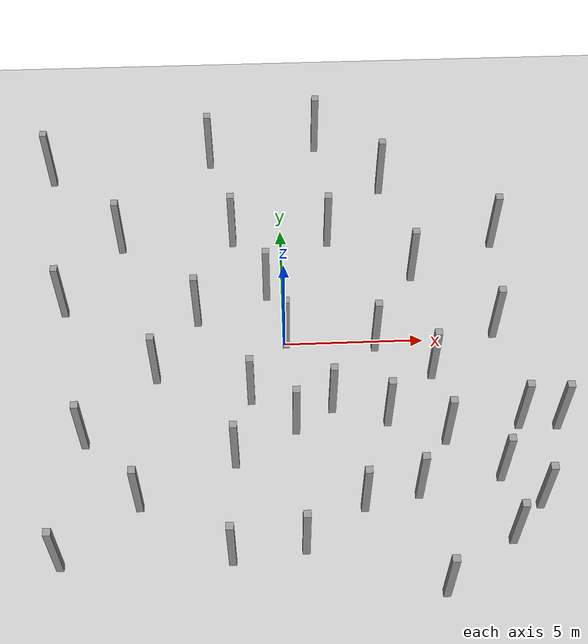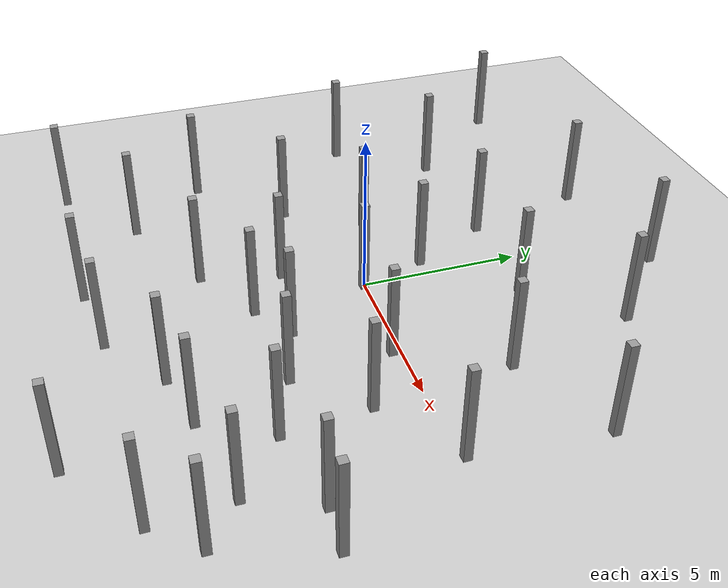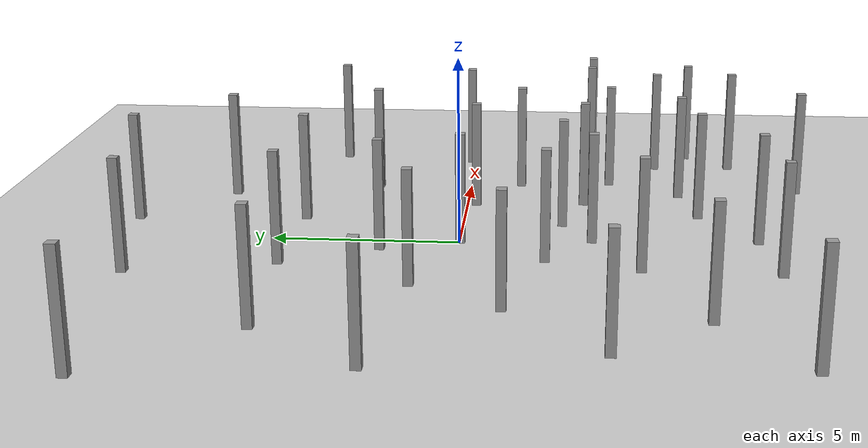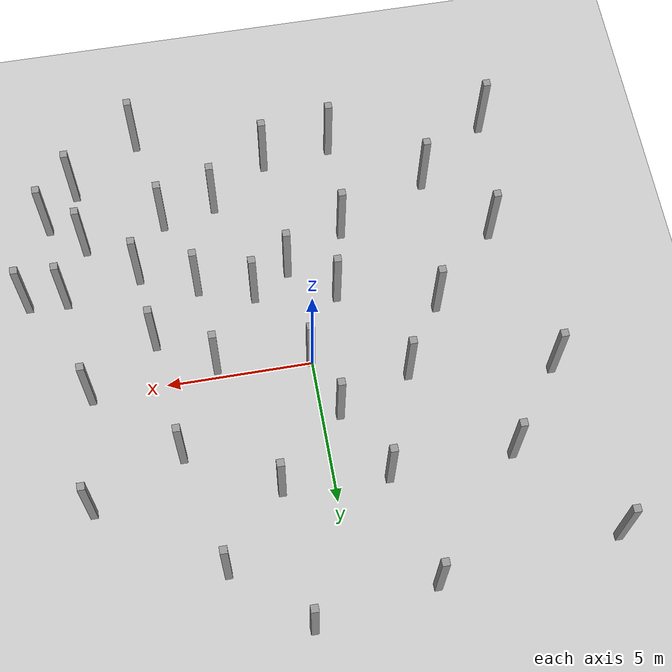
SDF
<sdf version="1.6">
 <world name="default">
  <light name="sun" type="directional">
   <pose>0 0 10 0 -0 0</pose>
   <diffuse>0.8 0.8 0.8 1</diffuse>
   <specular>0.1 0.1 0.1 1</specular>
   <attenuation>
    <range>1000</range>
    <constant>0.9</constant>
    <linear>0.01</linear>
    <quadratic>0.001</quadratic>
   </attenuation>
   <direction>-0.5 0.5 -1</direction>
  </light>
  <model name="ground_plane">
   <static>1</static>
   <link name="link">
    <collision name="collision">
     <geometry><plane><normal>0 0 1</normal><size>100 100</size></plane></geometry>
     <surface><friction><ode><mu>100</mu><mu2>50</mu2></ode></friction></surface>
    </collision>
    <visual name="visual">
     <cast_shadows>0</cast_shadows>
     <geometry><plane><normal>0 0 1</normal><size>100 100</size></plane></geometry>
     <material>
      <script><uri>file://media/materials/scripts/gazebo.material</uri><name>Gazebo/Grey</name></script>
     </material>
    </visual>
   </link>
  </model>
  <gravity>0 0 -9.8</gravity>
  <magnetic_field>6e-06 2.3e-05 -4.2e-05</magnetic_field>
  <atmosphere type="adiabatic"/>
  <physics name="default_physics" default="0" type="ode">
   <max_step_size>0.001</max_step_size>
   <real_time_factor>1</real_time_factor>
   <real_time_update_rate>1000</real_time_update_rate>
  </physics>
  <scene><ambient>0.4 0.4 0.4 1</ambient><background>0.7 0.7 0.7 1</background><shadows>1</shadows></scene>
  <spherical_coordinates>
   <surface_model>EARTH_WGS84</surface_model>
   <latitude_deg>0</latitude_deg>
   <longitude_deg>0</longitude_deg>
   <elevation>0</elevation>
   <heading_deg>0</heading_deg>
  </spherical_coordinates>
  <model name="box_2">
   <link name="link">
    <pose>0 0 1 0 -0 0</pose>
    <inertial>
     <mass>1</mass>
     <inertia><ixx>5.16667</ixx><ixy>0</ixy><ixz>0</ixz><iyy>5.16667</iyy><iyz>0</iyz><izz>5.16667</izz></inertia>
     <pose>0 0 1 0 -0 0</pose>
    </inertial>
    <visual name="ModelPreview_4::link::visual_1">
     <geometry><box><size>0.25 0.25 3</size></box></geometry>
     <material>
      <script><name>Gazebo/Grey</name><uri>file://media/materials/scripts/gazebo.material</uri></script>
      <ambient>0.3 0.3 0.3 1</ambient>
      <diffuse>0.7 0.7 0.7 1</diffuse>
      <specular>0.01 0.01 0.01 1</specular>
      <emissive>0 0 0 1</emissive>
      <shader type="vertex"><normal_map>__default__</normal_map></shader>
     </material>
    </visual>
    <visual name="visual">
     <geometry><box><size>0.25 0.25 3</size></box></geometry>
     <material>
      <script><name>Gazebo/Grey</name><uri>file://media/materials/scripts/gazebo.material</uri></script>
      <ambient>0.3 0.3 0.3 1</ambient>
      <diffuse>0.7 0.7 0.7 1</diffuse>
      <specular>0.01 0.01 0.01 1</specular>
      <emissive>0 0 0 1</emissive>
      <shader type="vertex"><normal_map>__default__</normal_map></shader>
     </material>
    </visual>
    <collision name="collision">
     <geometry><box><size>0.25 0.25 3</size></box></geometry>
     <surface>
      <friction>
       <ode><mu>1</mu><mu2>1</mu2><fdir1>0 0 0</fdir1><slip1>0</slip1><slip2>0</slip2></ode>
       <torsional>
        <coefficient>1</coefficient>
        <patch_radius>0</patch_radius>
        <surface_radius>0</surface_radius>
        <use_patch_radius>1</use_patch_radius>
        <ode><slip>0</slip></ode>
       </torsional>
      </friction>
      <bounce><restitution_coefficient>0</restitution_coefficient><threshold>1e+06</threshold></bounce>
      <contact>
       <collide_without_contact>0</collide_without_contact>
       <collide_without_contact_bitmask>1</collide_without_contact_bitmask>
       <collide_bitmask>1</collide_bitmask>
       <ode>
        <soft_cfm>0</soft_cfm>
        <soft_erp>0.2</soft_erp>
        <kp>1e+13</kp>
        <kd>1</kd>
        <max_vel>0.01</max_vel>
        <min_depth>0</min_depth>
       </ode>
       <bullet>
        <split_impulse>1</split_impulse>
        <split_impulse_penetration_threshold>-0.01</split_impulse_penetration_threshold>
        <soft_cfm>0</soft_cfm>
        <soft_erp>0.2</soft_erp>
        <kp>1e+13</kp>
        <kd>1</kd>
       </bullet>
      </contact>
     </surface>
    </collision>
   </link>
   <static>0</static>
   <pose>0.066026 -0.031786 0.49999 0 -1e-06 -0.000159</pose>
  </model>
  <model name="box_2_0">
   <link name="link">
    <pose>0 0 1 0 -0 0</pose>
    <inertial>
     <mass>1</mass>
     <inertia><ixx>5.16667</ixx><ixy>0</ixy><ixz>0</ixz><iyy>5.16667</iyy><iyz>0</iyz><izz>5.16667</izz></inertia>
     <pose>0 0 1 0 -0 0</pose>
    </inertial>
    <visual name="ModelPreview_4::link::visual_1">
     <geometry><box><size>0.25 0.25 3</size></box></geometry>
     <material>
      <script><name>Gazebo/Grey</name><uri>file://media/materials/scripts/gazebo.material</uri></script>
      <ambient>0.3 0.3 0.3 1</ambient>
      <diffuse>0.7 0.7 0.7 1</diffuse>
      <specular>0.01 0.01 0.01 1</specular>
      <emissive>0 0 0 1</emissive>
      <shader type="vertex"><normal_map>__default__</normal_map></shader>
     </material>
    </visual>
    <visual name="visual">
     <geometry><box><size>0.25 0.25 3</size></box></geometry>
     <material>
      <script><name>Gazebo/Grey</name><uri>file://media/materials/scripts/gazebo.material</uri></script>
      <ambient>0.3 0.3 0.3 1</ambient>
      <diffuse>0.7 0.7 0.7 1</diffuse>
      <specular>0.01 0.01 0.01 1</specular>
      <emissive>0 0 0 1</emissive>
      <shader type="vertex"><normal_map>__default__</normal_map></shader>
     </material>
    </visual>
    <collision name="collision">
     <geometry><box><size>0.25 0.25 3</size></box></geometry>
     <surface>
      <friction>
       <ode><mu>1</mu><mu2>1</mu2><fdir1>0 0 0</fdir1><slip1>0</slip1><slip2>0</slip2></ode>
       <torsional>
        <coefficient>1</coefficient>
        <patch_radius>0</patch_radius>
        <surface_radius>0</surface_radius>
        <use_patch_radius>1</use_patch_radius>
        <ode><slip>0</slip></ode>
       </torsional>
      </friction>
      <bounce><restitution_coefficient>0</restitution_coefficient><threshold>1e+06</threshold></bounce>
      <contact>
       <collide_without_contact>0</collide_without_contact>
       <collide_without_contact_bitmask>1</collide_without_contact_bitmask>
       <collide_bitmask>1</collide_bitmask>
       <ode>
        <soft_cfm>0</soft_cfm>
        <soft_erp>0.2</soft_erp>
        <kp>1e+13</kp>
        <kd>1</kd>
        <max_vel>0.01</max_vel>
        <min_depth>0</min_depth>
       </ode>
       <bullet>
        <split_impulse>1</split_impulse>
        <split_impulse_penetration_threshold>-0.01</split_impulse_penetration_threshold>
        <soft_cfm>0</soft_cfm>
        <soft_erp>0.2</soft_erp>
        <kp>1e+13</kp>
        <kd>1</kd>
       </bullet>
      </contact>
     </surface>
    </collision>
   </link>
   <static>0</static>
   <pose>-1.80227 -4.75192 0.5 -3e-06 -1e-06 -0.000128</pose>
  </model>
  <model name="box_2_1">
   <link name="link">
    <pose>0 0 1 0 -0 0</pose>
    <inertial>
     <mass>1</mass>
     <inertia><ixx>5.16667</ixx><ixy>0</ixy><ixz>0</ixz><iyy>5.16667</iyy><iyz>0</iyz><izz>5.16667</izz></inertia>
     <pose>0 0 1 0 -0 0</pose>
    </inertial>
    <visual name="ModelPreview_4::link::visual_1">
     <geometry><box><size>0.25 0.25 3</size></box></geometry>
     <material>
      <script><name>Gazebo/Grey</name><uri>file://media/materials/scripts/gazebo.material</uri></script>
      <ambient>0.3 0.3 0.3 1</ambient>
      <diffuse>0.7 0.7 0.7 1</diffuse>
      <specular>0.01 0.01 0.01 1</specular>
      <emissive>0 0 0 1</emissive>
      <shader type="vertex"><normal_map>__default__</normal_map></shader>
     </material>
    </visual>
    <visual name="visual">
     <geometry><box><size>0.25 0.25 3</size></box></geometry>
     <material>
      <script><name>Gazebo/Grey</name><uri>file://media/materials/scripts/gazebo.material</uri></script>
      <ambient>0.3 0.3 0.3 1</ambient>
      <diffuse>0.7 0.7 0.7 1</diffuse>
      <specular>0.01 0.01 0.01 1</specular>
      <emissive>0 0 0 1</emissive>
      <shader type="vertex"><normal_map>__default__</normal_map></shader>
     </material>
    </visual>
    <collision name="collision">
     <geometry><box><size>0.25 0.25 3</size></box></geometry>
     <surface>
      <friction>
       <ode><mu>1</mu><mu2>1</mu2><fdir1>0 0 0</fdir1><slip1>0</slip1><slip2>0</slip2></ode>
       <torsional>
        <coefficient>1</coefficient>
        <patch_radius>0</patch_radius>
        <surface_radius>0</surface_radius>
        <use_patch_radius>1</use_patch_radius>
        <ode><slip>0</slip></ode>
       </torsional>
      </friction>
      <bounce><restitution_coefficient>0</restitution_coefficient><threshold>1e+06</threshold></bounce>
      <contact>
       <collide_without_contact>0</collide_without_contact>
       <collide_without_contact_bitmask>1</collide_without_contact_bitmask>
       <collide_bitmask>1</collide_bitmask>
       <ode>
        <soft_cfm>0</soft_cfm>
        <soft_erp>0.2</soft_erp>
        <kp>1e+13</kp>
        <kd>1</kd>
        <max_vel>0.01</max_vel>
        <min_depth>0</min_depth>
       </ode>
       <bullet>
        <split_impulse>1</split_impulse>
        <split_impulse_penetration_threshold>-0.01</split_impulse_penetration_threshold>
        <soft_cfm>0</soft_cfm>
        <soft_erp>0.2</soft_erp>
        <kp>1e+13</kp>
        <kd>1</kd>
       </bullet>
      </contact>
     </surface>
    </collision>
   </link>
   <static>0</static>
   <pose>4.35883 -6.08967 0.500001 0 5e-06 -0.000185</pose>
  </model>
  <model name="box_2_2">
   <link name="link">
    <pose>0 0 1 0 -0 0</pose>
    <inertial>
     <mass>1</mass>
     <inertia><ixx>5.16667</ixx><ixy>0</ixy><ixz>0</ixz><iyy>5.16667</iyy><iyz>0</iyz><izz>5.16667</izz></inertia>
     <pose>0 0 1 0 -0 0</pose>
    </inertial>
    <visual name="ModelPreview_4::link::visual_1">
     <geometry><box><size>0.25 0.25 3</size></box></geometry>
     <material>
      <script><name>Gazebo/Grey</name><uri>file://media/materials/scripts/gazebo.material</uri></script>
      <ambient>0.3 0.3 0.3 1</ambient>
      <diffuse>0.7 0.7 0.7 1</diffuse>
      <specular>0.01 0.01 0.01 1</specular>
      <emissive>0 0 0 1</emissive>
      <shader type="vertex"><normal_map>__default__</normal_map></shader>
     </material>
    </visual>
    <visual name="visual">
     <geometry><box><size>0.25 0.25 3</size></box></geometry>
     <material>
      <script><name>Gazebo/Grey</name><uri>file://media/materials/scripts/gazebo.material</uri></script>
      <ambient>0.3 0.3 0.3 1</ambient>
      <diffuse>0.7 0.7 0.7 1</diffuse>
      <specular>0.01 0.01 0.01 1</specular>
      <emissive>0 0 0 1</emissive>
      <shader type="vertex"><normal_map>__default__</normal_map></shader>
     </material>
    </visual>
    <collision name="collision">
     <geometry><box><size>0.25 0.25 3</size></box></geometry>
     <surface>
      <friction>
       <ode><mu>1</mu><mu2>1</mu2><fdir1>0 0 0</fdir1><slip1>0</slip1><slip2>0</slip2></ode>
       <torsional>
        <coefficient>1</coefficient>
        <patch_radius>0</patch_radius>
        <surface_radius>0</surface_radius>
        <use_patch_radius>1</use_patch_radius>
        <ode><slip>0</slip></ode>
       </torsional>
      </friction>
      <bounce><restitution_coefficient>0</restitution_coefficient><threshold>1e+06</threshold></bounce>
      <contact>
       <collide_without_contact>0</collide_without_contact>
       <collide_without_contact_bitmask>1</collide_without_contact_bitmask>
       <collide_bitmask>1</collide_bitmask>
       <ode>
        <soft_cfm>0</soft_cfm>
        <soft_erp>0.2</soft_erp>
        <kp>1e+13</kp>
        <kd>1</kd>
        <max_vel>0.01</max_vel>
        <min_depth>0</min_depth>
       </ode>
       <bullet>
        <split_impulse>1</split_impulse>
        <split_impulse_penetration_threshold>-0.01</split_impulse_penetration_threshold>
        <soft_cfm>0</soft_cfm>
        <soft_erp>0.2</soft_erp>
        <kp>1e+13</kp>
        <kd>1</kd>
       </bullet>
      </contact>
     </surface>
    </collision>
   </link>
   <static>0</static>
   <pose>7.18492 -5.54152 0.5 0 1e-06 -0.000157</pose>
  </model>
  <model name="box_2_3">
   <link name="link">
    <pose>0 0 1 0 -0 0</pose>
    <inertial>
     <mass>1</mass>
     <inertia><ixx>5.16667</ixx><ixy>0</ixy><ixz>0</ixz><iyy>5.16667</iyy><iyz>0</iyz><izz>5.16667</izz></inertia>
     <pose>0 0 1 0 -0 0</pose>
    </inertial>
    <visual name="ModelPreview_4::link::visual_1">
     <geometry><box><size>0.25 0.25 3</size></box></geometry>
     <material>
      <script><name>Gazebo/Grey</name><uri>file://media/materials/scripts/gazebo.material</uri></script>
      <ambient>0.3 0.3 0.3 1</ambient>
      <diffuse>0.7 0.7 0.7 1</diffuse>
      <specular>0.01 0.01 0.01 1</specular>
      <emissive>0 0 0 1</emissive>
      <shader type="vertex"><normal_map>__default__</normal_map></shader>
     </material>
    </visual>
    <visual name="visual">
     <geometry><box><size>0.25 0.25 3</size></box></geometry>
     <material>
      <script><name>Gazebo/Grey</name><uri>file://media/materials/scripts/gazebo.material</uri></script>
      <ambient>0.3 0.3 0.3 1</ambient>
      <diffuse>0.7 0.7 0.7 1</diffuse>
      <specular>0.01 0.01 0.01 1</specular>
      <emissive>0 0 0 1</emissive>
      <shader type="vertex"><normal_map>__default__</normal_map></shader>
     </material>
    </visual>
    <collision name="collision">
     <geometry><box><size>0.25 0.25 3</size></box></geometry>
     <surface>
      <friction>
       <ode><mu>1</mu><mu2>1</mu2><fdir1>0 0 0</fdir1><slip1>0</slip1><slip2>0</slip2></ode>
       <torsional>
        <coefficient>1</coefficient>
        <patch_radius>0</patch_radius>
        <surface_radius>0</surface_radius>
        <use_patch_radius>1</use_patch_radius>
        <ode><slip>0</slip></ode>
       </torsional>
      </friction>
      <bounce><restitution_coefficient>0</restitution_coefficient><threshold>1e+06</threshold></bounce>
      <contact>
       <collide_without_contact>0</collide_without_contact>
       <collide_without_contact_bitmask>1</collide_without_contact_bitmask>
       <collide_bitmask>1</collide_bitmask>
       <ode>
        <soft_cfm>0</soft_cfm>
        <soft_erp>0.2</soft_erp>
        <kp>1e+13</kp>
        <kd>1</kd>
        <max_vel>0.01</max_vel>
        <min_depth>0</min_depth>
       </ode>
       <bullet>
        <split_impulse>1</split_impulse>
        <split_impulse_penetration_threshold>-0.01</split_impulse_penetration_threshold>
        <soft_cfm>0</soft_cfm>
        <soft_erp>0.2</soft_erp>
        <kp>1e+13</kp>
        <kd>1</kd>
       </bullet>
      </contact>
     </surface>
    </collision>
   </link>
   <static>0</static>
   <pose>0.476728 -7.9552 0.500001 3e-06 -4e-06 -0.000167</pose>
  </model>
  <model name="box_2_4">
   <link name="link">
    <pose>0 0 1 0 -0 0</pose>
    <inertial>
     <mass>1</mass>
     <inertia><ixx>5.16667</ixx><ixy>0</ixy><ixz>0</ixz><iyy>5.16667</iyy><iyz>0</iyz><izz>5.16667</izz></inertia>
     <pose>0 0 1 0 -0 0</pose>
    </inertial>
    <visual name="ModelPreview_4::link::visual_1">
     <geometry><box><size>0.25 0.25 3</size></box></geometry>
     <material>
      <script><name>Gazebo/Grey</name><uri>file://media/materials/scripts/gazebo.material</uri></script>
      <ambient>0.3 0.3 0.3 1</ambient>
      <diffuse>0.7 0.7 0.7 1</diffuse>
      <specular>0.01 0.01 0.01 1</specular>
      <emissive>0 0 0 1</emissive>
      <shader type="vertex"><normal_map>__default__</normal_map></shader>
     </material>
    </visual>
    <visual name="visual">
     <geometry><box><size>0.25 0.25 3</size></box></geometry>
     <material>
      <script><name>Gazebo/Grey</name><uri>file://media/materials/scripts/gazebo.material</uri></script>
      <ambient>0.3 0.3 0.3 1</ambient>
      <diffuse>0.7 0.7 0.7 1</diffuse>
      <specular>0.01 0.01 0.01 1</specular>
      <emissive>0 0 0 1</emissive>
      <shader type="vertex"><normal_map>__default__</normal_map></shader>
     </material>
    </visual>
    <collision name="collision">
     <geometry><box><size>0.25 0.25 3</size></box></geometry>
     <surface>
      <friction>
       <ode><mu>1</mu><mu2>1</mu2><fdir1>0 0 0</fdir1><slip1>0</slip1><slip2>0</slip2></ode>
       <torsional>
        <coefficient>1</coefficient>
        <patch_radius>0</patch_radius>
        <surface_radius>0</surface_radius>
        <use_patch_radius>1</use_patch_radius>
        <ode><slip>0</slip></ode>
       </torsional>
      </friction>
      <bounce><restitution_coefficient>0</restitution_coefficient><threshold>1e+06</threshold></bounce>
      <contact>
       <collide_without_contact>0</collide_without_contact>
       <collide_without_contact_bitmask>1</collide_without_contact_bitmask>
       <collide_bitmask>1</collide_bitmask>
       <ode>
        <soft_cfm>0</soft_cfm>
        <soft_erp>0.2</soft_erp>
        <kp>1e+13</kp>
        <kd>1</kd>
        <max_vel>0.01</max_vel>
        <min_depth>0</min_depth>
       </ode>
       <bullet>
        <split_impulse>1</split_impulse>
        <split_impulse_penetration_threshold>-0.01</split_impulse_penetration_threshold>
        <soft_cfm>0</soft_cfm>
        <soft_erp>0.2</soft_erp>
        <kp>1e+13</kp>
        <kd>1</kd>
       </bullet>
      </contact>
     </surface>
    </collision>
   </link>
   <static>0</static>
   <pose>7.33014 -7.82542 0.5 3e-06 -0 -0.000129</pose>
  </model>
  <model name="box_2_5">
   <link name="link">
    <pose>0 0 1 0 -0 0</pose>
    <inertial>
     <mass>1</mass>
     <inertia><ixx>5.16667</ixx><ixy>0</ixy><ixz>0</ixz><iyy>5.16667</iyy><iyz>0</iyz><izz>5.16667</izz></inertia>
     <pose>0 0 1 0 -0 0</pose>
    </inertial>
    <visual name="ModelPreview_4::link::visual_1">
     <geometry><box><size>0.25 0.25 3</size></box></geometry>
     <material>
      <script><name>Gazebo/Grey</name><uri>file://media/materials/scripts/gazebo.material</uri></script>
      <ambient>0.3 0.3 0.3 1</ambient>
      <diffuse>0.7 0.7 0.7 1</diffuse>
      <specular>0.01 0.01 0.01 1</specular>
      <emissive>0 0 0 1</emissive>
      <shader type="vertex"><normal_map>__default__</normal_map></shader>
     </material>
    </visual>
    <visual name="visual">
     <geometry><box><size>0.25 0.25 3</size></box></geometry>
     <material>
      <script><name>Gazebo/Grey</name><uri>file://media/materials/scripts/gazebo.material</uri></script>
      <ambient>0.3 0.3 0.3 1</ambient>
      <diffuse>0.7 0.7 0.7 1</diffuse>
      <specular>0.01 0.01 0.01 1</specular>
      <emissive>0 0 0 1</emissive>
      <shader type="vertex"><normal_map>__default__</normal_map></shader>
     </material>
    </visual>
    <collision name="collision">
     <geometry><box><size>0.25 0.25 3</size></box></geometry>
     <surface>
      <friction>
       <ode><mu>1</mu><mu2>1</mu2><fdir1>0 0 0</fdir1><slip1>0</slip1><slip2>0</slip2></ode>
       <torsional>
        <coefficient>1</coefficient>
        <patch_radius>0</patch_radius>
        <surface_radius>0</surface_radius>
        <use_patch_radius>1</use_patch_radius>
        <ode><slip>0</slip></ode>
       </torsional>
      </friction>
      <bounce><restitution_coefficient>0</restitution_coefficient><threshold>1e+06</threshold></bounce>
      <contact>
       <collide_without_contact>0</collide_without_contact>
       <collide_without_contact_bitmask>1</collide_without_contact_bitmask>
       <collide_bitmask>1</collide_bitmask>
       <ode>
        <soft_cfm>0</soft_cfm>
        <soft_erp>0.2</soft_erp>
        <kp>1e+13</kp>
        <kd>1</kd>
        <max_vel>0.01</max_vel>
        <min_depth>0</min_depth>
       </ode>
       <bullet>
        <split_impulse>1</split_impulse>
        <split_impulse_penetration_threshold>-0.01</split_impulse_penetration_threshold>
        <soft_cfm>0</soft_cfm>
        <soft_erp>0.2</soft_erp>
        <kp>1e+13</kp>
        <kd>1</kd>
       </bullet>
      </contact>
     </surface>
    </collision>
   </link>
   <static>0</static>
   <pose>7.55225 0.161645 0.5 0 0 -9.9e-05</pose>
  </model>
  <model name="box_2_6">
   <link name="link">
    <pose>0 0 1 0 -0 0</pose>
    <inertial>
     <mass>1</mass>
     <inertia><ixx>5.16667</ixx><ixy>0</ixy><ixz>0</ixz><iyy>5.16667</iyy><iyz>0</iyz><izz>5.16667</izz></inertia>
     <pose>0 0 1 0 -0 0</pose>
    </inertial>
    <visual name="ModelPreview_4::link::visual_1">
     <geometry><box><size>0.25 0.25 3</size></box></geometry>
     <material>
      <script><name>Gazebo/Grey</name><uri>file://media/materials/scripts/gazebo.material</uri></script>
      <ambient>0.3 0.3 0.3 1</ambient>
      <diffuse>0.7 0.7 0.7 1</diffuse>
      <specular>0.01 0.01 0.01 1</specular>
      <emissive>0 0 0 1</emissive>
      <shader type="vertex"><normal_map>__default__</normal_map></shader>
     </material>
    </visual>
    <visual name="visual">
     <geometry><box><size>0.25 0.25 3</size></box></geometry>
     <material>
      <script><name>Gazebo/Grey</name><uri>file://media/materials/scripts/gazebo.material</uri></script>
      <ambient>0.3 0.3 0.3 1</ambient>
      <diffuse>0.7 0.7 0.7 1</diffuse>
      <specular>0.01 0.01 0.01 1</specular>
      <emissive>0 0 0 1</emissive>
      <shader type="vertex"><normal_map>__default__</normal_map></shader>
     </material>
    </visual>
    <collision name="collision">
     <geometry><box><size>0.25 0.25 3</size></box></geometry>
     <surface>
      <friction>
       <ode><mu>1</mu><mu2>1</mu2><fdir1>0 0 0</fdir1><slip1>0</slip1><slip2>0</slip2></ode>
       <torsional>
        <coefficient>1</coefficient>
        <patch_radius>0</patch_radius>
        <surface_radius>0</surface_radius>
        <use_patch_radius>1</use_patch_radius>
        <ode><slip>0</slip></ode>
       </torsional>
      </friction>
      <bounce><restitution_coefficient>0</restitution_coefficient><threshold>1e+06</threshold></bounce>
      <contact>
       <collide_without_contact>0</collide_without_contact>
       <collide_without_contact_bitmask>1</collide_without_contact_bitmask>
       <collide_bitmask>1</collide_bitmask>
       <ode>
        <soft_cfm>0</soft_cfm>
        <soft_erp>0.2</soft_erp>
        <kp>1e+13</kp>
        <kd>1</kd>
        <max_vel>0.01</max_vel>
        <min_depth>0</min_depth>
       </ode>
       <bullet>
        <split_impulse>1</split_impulse>
        <split_impulse_penetration_threshold>-0.01</split_impulse_penetration_threshold>
        <soft_cfm>0</soft_cfm>
        <soft_erp>0.2</soft_erp>
        <kp>1e+13</kp>
        <kd>1</kd>
       </bullet>
      </contact>
     </surface>
    </collision>
   </link>
   <static>0</static>
   <pose>3.49181 -3.31679 0.5 1e-06 -3e-06 -9.3e-05</pose>
  </model>
  <model name="box_2_7">
   <link name="link">
    <pose>0 0 1 0 -0 0</pose>
    <inertial>
     <mass>1</mass>
     <inertia><ixx>5.16667</ixx><ixy>0</ixy><ixz>0</ixz><iyy>5.16667</iyy><iyz>0</iyz><izz>5.16667</izz></inertia>
     <pose>0 0 1 0 -0 0</pose>
    </inertial>
    <visual name="ModelPreview_4::link::visual_1">
     <geometry><box><size>0.25 0.25 3</size></box></geometry>
     <material>
      <script><name>Gazebo/Grey</name><uri>file://media/materials/scripts/gazebo.material</uri></script>
      <ambient>0.3 0.3 0.3 1</ambient>
      <diffuse>0.7 0.7 0.7 1</diffuse>
      <specular>0.01 0.01 0.01 1</specular>
      <emissive>0 0 0 1</emissive>
      <shader type="vertex"><normal_map>__default__</normal_map></shader>
     </material>
    </visual>
    <visual name="visual">
     <geometry><box><size>0.25 0.25 3</size></box></geometry>
     <material>
      <script><name>Gazebo/Grey</name><uri>file://media/materials/scripts/gazebo.material</uri></script>
      <ambient>0.3 0.3 0.3 1</ambient>
      <diffuse>0.7 0.7 0.7 1</diffuse>
      <specular>0.01 0.01 0.01 1</specular>
      <emissive>0 0 0 1</emissive>
      <shader type="vertex"><normal_map>__default__</normal_map></shader>
     </material>
    </visual>
    <collision name="collision">
     <geometry><box><size>0.25 0.25 3</size></box></geometry>
     <surface>
      <friction>
       <ode><mu>1</mu><mu2>1</mu2><fdir1>0 0 0</fdir1><slip1>0</slip1><slip2>0</slip2></ode>
       <torsional>
        <coefficient>1</coefficient>
        <patch_radius>0</patch_radius>
        <surface_radius>0</surface_radius>
        <use_patch_radius>1</use_patch_radius>
        <ode><slip>0</slip></ode>
       </torsional>
      </friction>
      <bounce><restitution_coefficient>0</restitution_coefficient><threshold>1e+06</threshold></bounce>
      <contact>
       <collide_without_contact>0</collide_without_contact>
       <collide_without_contact_bitmask>1</collide_without_contact_bitmask>
       <collide_bitmask>1</collide_bitmask>
       <ode>
        <soft_cfm>0</soft_cfm>
        <soft_erp>0.2</soft_erp>
        <kp>1e+13</kp>
        <kd>1</kd>
        <max_vel>0.01</max_vel>
        <min_depth>0</min_depth>
       </ode>
       <bullet>
        <split_impulse>1</split_impulse>
        <split_impulse_penetration_threshold>-0.01</split_impulse_penetration_threshold>
        <soft_cfm>0</soft_cfm>
        <soft_erp>0.2</soft_erp>
        <kp>1e+13</kp>
        <kd>1</kd>
       </bullet>
      </contact>
     </surface>
    </collision>
   </link>
   <static>0</static>
   <pose>-1.22637 -2.30478 0.500002 -1.7e-05 1e-06 -0.000177</pose>
  </model>
  <model name="box_2_8">
   <link name="link">
    <pose>0 0 1 0 -0 0</pose>
    <inertial>
     <mass>1</mass>
     <inertia><ixx>5.16667</ixx><ixy>0</ixy><ixz>0</ixz><iyy>5.16667</iyy><iyz>0</iyz><izz>5.16667</izz></inertia>
     <pose>0 0 1 0 -0 0</pose>
    </inertial>
    <visual name="ModelPreview_4::link::visual_1">
     <geometry><box><size>0.25 0.25 3</size></box></geometry>
     <material>
      <script><name>Gazebo/Grey</name><uri>file://media/materials/scripts/gazebo.material</uri></script>
      <ambient>0.3 0.3 0.3 1</ambient>
      <diffuse>0.7 0.7 0.7 1</diffuse>
      <specular>0.01 0.01 0.01 1</specular>
      <emissive>0 0 0 1</emissive>
      <shader type="vertex"><normal_map>__default__</normal_map></shader>
     </material>
    </visual>
    <visual name="visual">
     <geometry><box><size>0.25 0.25 3</size></box></geometry>
     <material>
      <script><name>Gazebo/Grey</name><uri>file://media/materials/scripts/gazebo.material</uri></script>
      <ambient>0.3 0.3 0.3 1</ambient>
      <diffuse>0.7 0.7 0.7 1</diffuse>
      <specular>0.01 0.01 0.01 1</specular>
      <emissive>0 0 0 1</emissive>
      <shader type="vertex"><normal_map>__default__</normal_map></shader>
     </material>
    </visual>
    <collision name="collision">
     <geometry><box><size>0.25 0.25 3</size></box></geometry>
     <surface>
      <friction>
       <ode><mu>1</mu><mu2>1</mu2><fdir1>0 0 0</fdir1><slip1>0</slip1><slip2>0</slip2></ode>
       <torsional>
        <coefficient>1</coefficient>
        <patch_radius>0</patch_radius>
        <surface_radius>0</surface_radius>
        <use_patch_radius>1</use_patch_radius>
        <ode><slip>0</slip></ode>
       </torsional>
      </friction>
      <bounce><restitution_coefficient>0</restitution_coefficient><threshold>1e+06</threshold></bounce>
      <contact>
       <collide_without_contact>0</collide_without_contact>
       <collide_without_contact_bitmask>1</collide_without_contact_bitmask>
       <collide_bitmask>1</collide_bitmask>
       <ode>
        <soft_cfm>0</soft_cfm>
        <soft_erp>0.2</soft_erp>
        <kp>1e+13</kp>
        <kd>1</kd>
        <max_vel>0.01</max_vel>
        <min_depth>0</min_depth>
       </ode>
       <bullet>
        <split_impulse>1</split_impulse>
        <split_impulse_penetration_threshold>-0.01</split_impulse_penetration_threshold>
        <soft_cfm>0</soft_cfm>
        <soft_erp>0.2</soft_erp>
        <kp>1e+13</kp>
        <kd>1</kd>
       </bullet>
      </contact>
     </surface>
    </collision>
   </link>
   <static>0</static>
   <pose>2.49951 -6.51199 0.5 0 0 -0.000133</pose>
  </model>
  <model name="box_2_9">
   <link name="link">
    <pose>0 0 1 0 -0 0</pose>
    <inertial>
     <mass>1</mass>
     <inertia><ixx>5.16667</ixx><ixy>0</ixy><ixz>0</ixz><iyy>5.16667</iyy><iyz>0</iyz><izz>5.16667</izz></inertia>
     <pose>0 0 1 0 -0 0</pose>
    </inertial>
    <visual name="ModelPreview_4::link::visual_1">
     <geometry><box><size>0.25 0.25 3</size></box></geometry>
     <material>
      <script><name>Gazebo/Grey</name><uri>file://media/materials/scripts/gazebo.material</uri></script>
      <ambient>0.3 0.3 0.3 1</ambient>
      <diffuse>0.7 0.7 0.7 1</diffuse>
      <specular>0.01 0.01 0.01 1</specular>
      <emissive>0 0 0 1</emissive>
      <shader type="vertex"><normal_map>__default__</normal_map></shader>
     </material>
    </visual>
    <visual name="visual">
     <geometry><box><size>0.25 0.25 3</size></box></geometry>
     <material>
      <script><name>Gazebo/Grey</name><uri>file://media/materials/scripts/gazebo.material</uri></script>
      <ambient>0.3 0.3 0.3 1</ambient>
      <diffuse>0.7 0.7 0.7 1</diffuse>
      <specular>0.01 0.01 0.01 1</specular>
      <emissive>0 0 0 1</emissive>
      <shader type="vertex"><normal_map>__default__</normal_map></shader>
     </material>
    </visual>
    <collision name="collision">
     <geometry><box><size>0.25 0.25 3</size></box></geometry>
     <surface>
      <friction>
       <ode><mu>1</mu><mu2>1</mu2><fdir1>0 0 0</fdir1><slip1>0</slip1><slip2>0</slip2></ode>
       <torsional>
        <coefficient>1</coefficient>
        <patch_radius>0</patch_radius>
        <surface_radius>0</surface_radius>
        <use_patch_radius>1</use_patch_radius>
        <ode><slip>0</slip></ode>
       </torsional>
      </friction>
      <bounce><restitution_coefficient>0</restitution_coefficient><threshold>1e+06</threshold></bounce>
      <contact>
       <collide_without_contact>0</collide_without_contact>
       <collide_without_contact_bitmask>1</collide_without_contact_bitmask>
       <collide_bitmask>1</collide_bitmask>
       <ode>
        <soft_cfm>0</soft_cfm>
        <soft_erp>0.2</soft_erp>
        <kp>1e+13</kp>
        <kd>1</kd>
        <max_vel>0.01</max_vel>
        <min_depth>0</min_depth>
       </ode>
       <bullet>
        <split_impulse>1</split_impulse>
        <split_impulse_penetration_threshold>-0.01</split_impulse_penetration_threshold>
        <soft_cfm>0</soft_cfm>
        <soft_erp>0.2</soft_erp>
        <kp>1e+13</kp>
        <kd>1</kd>
       </bullet>
      </contact>
     </surface>
    </collision>
   </link>
   <static>0</static>
   <pose>-1.93996 -8.27565 0.5 -0 1e-06 -0.000136</pose>
  </model>
  <model name="box_2_10">
   <link name="link">
    <pose>0 0 1 0 -0 0</pose>
    <inertial>
     <mass>1</mass>
     <inertia><ixx>5.16667</ixx><ixy>0</ixy><ixz>0</ixz><iyy>5.16667</iyy><iyz>0</iyz><izz>5.16667</izz></inertia>
     <pose>0 0 1 0 -0 0</pose>
    </inertial>
    <visual name="ModelPreview_4::link::visual_1">
     <geometry><box><size>0.25 0.25 3</size></box></geometry>
     <material>
      <script><name>Gazebo/Grey</name><uri>file://media/materials/scripts/gazebo.material</uri></script>
      <ambient>0.3 0.3 0.3 1</ambient>
      <diffuse>0.7 0.7 0.7 1</diffuse>
      <specular>0.01 0.01 0.01 1</specular>
      <emissive>0 0 0 1</emissive>
      <shader type="vertex"><normal_map>__default__</normal_map></shader>
     </material>
    </visual>
    <visual name="visual">
     <geometry><box><size>0.25 0.25 3</size></box></geometry>
     <material>
      <script><name>Gazebo/Grey</name><uri>file://media/materials/scripts/gazebo.material</uri></script>
      <ambient>0.3 0.3 0.3 1</ambient>
      <diffuse>0.7 0.7 0.7 1</diffuse>
      <specular>0.01 0.01 0.01 1</specular>
      <emissive>0 0 0 1</emissive>
      <shader type="vertex"><normal_map>__default__</normal_map></shader>
     </material>
    </visual>
    <collision name="collision">
     <geometry><box><size>0.25 0.25 3</size></box></geometry>
     <surface>
      <friction>
       <ode><mu>1</mu><mu2>1</mu2><fdir1>0 0 0</fdir1><slip1>0</slip1><slip2>0</slip2></ode>
       <torsional>
        <coefficient>1</coefficient>
        <patch_radius>0</patch_radius>
        <surface_radius>0</surface_radius>
        <use_patch_radius>1</use_patch_radius>
        <ode><slip>0</slip></ode>
       </torsional>
      </friction>
      <bounce><restitution_coefficient>0</restitution_coefficient><threshold>1e+06</threshold></bounce>
      <contact>
       <collide_without_contact>0</collide_without_contact>
       <collide_without_contact_bitmask>1</collide_without_contact_bitmask>
       <collide_bitmask>1</collide_bitmask>
       <ode>
        <soft_cfm>0</soft_cfm>
        <soft_erp>0.2</soft_erp>
        <kp>1e+13</kp>
        <kd>1</kd>
        <max_vel>0.01</max_vel>
        <min_depth>0</min_depth>
       </ode>
       <bullet>
        <split_impulse>1</split_impulse>
        <split_impulse_penetration_threshold>-0.01</split_impulse_penetration_threshold>
        <soft_cfm>0</soft_cfm>
        <soft_erp>0.2</soft_erp>
        <kp>1e+13</kp>
        <kd>1</kd>
       </bullet>
      </contact>
     </surface>
    </collision>
   </link>
   <static>0</static>
   <pose>4.96375 -9.57303 0.500001 5e-06 -0 -0.000122</pose>
  </model>
  <model name="box_2_11">
   <link name="link">
    <pose>0 0 1 0 -0 0</pose>
    <inertial>
     <mass>1</mass>
     <inertia><ixx>5.16667</ixx><ixy>0</ixy><ixz>0</ixz><iyy>5.16667</iyy><iyz>0</iyz><izz>5.16667</izz></inertia>
     <pose>0 0 1 0 -0 0</pose>
    </inertial>
    <visual name="ModelPreview_4::link::visual_1">
     <geometry><box><size>0.25 0.25 3</size></box></geometry>
     <material>
      <script><name>Gazebo/Grey</name><uri>file://media/materials/scripts/gazebo.material</uri></script>
      <ambient>0.3 0.3 0.3 1</ambient>
      <diffuse>0.7 0.7 0.7 1</diffuse>
      <specular>0.01 0.01 0.01 1</specular>
      <emissive>0 0 0 1</emissive>
      <shader type="vertex"><normal_map>__default__</normal_map></shader>
     </material>
    </visual>
    <visual name="visual">
     <geometry><box><size>0.25 0.25 3</size></box></geometry>
     <material>
      <script><name>Gazebo/Grey</name><uri>file://media/materials/scripts/gazebo.material</uri></script>
      <ambient>0.3 0.3 0.3 1</ambient>
      <diffuse>0.7 0.7 0.7 1</diffuse>
      <specular>0.01 0.01 0.01 1</specular>
      <emissive>0 0 0 1</emissive>
      <shader type="vertex"><normal_map>__default__</normal_map></shader>
     </material>
    </visual>
    <collision name="collision">
     <geometry><box><size>0.25 0.25 3</size></box></geometry>
     <surface>
      <friction>
       <ode><mu>1</mu><mu2>1</mu2><fdir1>0 0 0</fdir1><slip1>0</slip1><slip2>0</slip2></ode>
       <torsional>
        <coefficient>1</coefficient>
        <patch_radius>0</patch_radius>
        <surface_radius>0</surface_radius>
        <use_patch_radius>1</use_patch_radius>
        <ode><slip>0</slip></ode>
       </torsional>
      </friction>
      <bounce><restitution_coefficient>0</restitution_coefficient><threshold>1e+06</threshold></bounce>
      <contact>
       <collide_without_contact>0</collide_without_contact>
       <collide_without_contact_bitmask>1</collide_without_contact_bitmask>
       <collide_bitmask>1</collide_bitmask>
       <ode>
        <soft_cfm>0</soft_cfm>
        <soft_erp>0.2</soft_erp>
        <kp>1e+13</kp>
        <kd>1</kd>
        <max_vel>0.01</max_vel>
        <min_depth>0</min_depth>
       </ode>
       <bullet>
        <split_impulse>1</split_impulse>
        <split_impulse_penetration_threshold>-0.01</split_impulse_penetration_threshold>
        <soft_cfm>0</soft_cfm>
        <soft_erp>0.2</soft_erp>
        <kp>1e+13</kp>
        <kd>1</kd>
       </bullet>
      </contact>
     </surface>
    </collision>
   </link>
   <static>0</static>
   <pose>-6.97607 -3.85239 0.500001 6e-06 0 -0.000115</pose>
  </model>
  <model name="box_2_12">
   <link name="link">
    <pose>0 0 1 0 -0 0</pose>
    <inertial>
     <mass>1</mass>
     <inertia><ixx>5.16667</ixx><ixy>0</ixy><ixz>0</ixz><iyy>5.16667</iyy><iyz>0</iyz><izz>5.16667</izz></inertia>
     <pose>0 0 1 0 -0 0</pose>
    </inertial>
    <visual name="ModelPreview_4::link::visual_1">
     <geometry><box><size>0.25 0.25 3</size></box></geometry>
     <material>
      <script><name>Gazebo/Grey</name><uri>file://media/materials/scripts/gazebo.material</uri></script>
      <ambient>0.3 0.3 0.3 1</ambient>
      <diffuse>0.7 0.7 0.7 1</diffuse>
      <specular>0.01 0.01 0.01 1</specular>
      <emissive>0 0 0 1</emissive>
      <shader type="vertex"><normal_map>__default__</normal_map></shader>
     </material>
    </visual>
    <visual name="visual">
     <geometry><box><size>0.25 0.25 3</size></box></geometry>
     <material>
      <script><name>Gazebo/Grey</name><uri>file://media/materials/scripts/gazebo.material</uri></script>
      <ambient>0.3 0.3 0.3 1</ambient>
      <diffuse>0.7 0.7 0.7 1</diffuse>
      <specular>0.01 0.01 0.01 1</specular>
      <emissive>0 0 0 1</emissive>
      <shader type="vertex"><normal_map>__default__</normal_map></shader>
     </material>
    </visual>
    <collision name="collision">
     <geometry><box><size>0.25 0.25 3</size></box></geometry>
     <surface>
      <friction>
       <ode><mu>1</mu><mu2>1</mu2><fdir1>0 0 0</fdir1><slip1>0</slip1><slip2>0</slip2></ode>
       <torsional>
        <coefficient>1</coefficient>
        <patch_radius>0</patch_radius>
        <surface_radius>0</surface_radius>
        <use_patch_radius>1</use_patch_radius>
        <ode><slip>0</slip></ode>
       </torsional>
      </friction>
      <bounce><restitution_coefficient>0</restitution_coefficient><threshold>1e+06</threshold></bounce>
      <contact>
       <collide_without_contact>0</collide_without_contact>
       <collide_without_contact_bitmask>1</collide_without_contact_bitmask>
       <collide_bitmask>1</collide_bitmask>
       <ode>
        <soft_cfm>0</soft_cfm>
        <soft_erp>0.2</soft_erp>
        <kp>1e+13</kp>
        <kd>1</kd>
        <max_vel>0.01</max_vel>
        <min_depth>0</min_depth>
       </ode>
       <bullet>
        <split_impulse>1</split_impulse>
        <split_impulse_penetration_threshold>-0.01</split_impulse_penetration_threshold>
        <soft_cfm>0</soft_cfm>
        <soft_erp>0.2</soft_erp>
        <kp>1e+13</kp>
        <kd>1</kd>
       </bullet>
      </contact>
     </surface>
    </collision>
   </link>
   <static>0</static>
   <pose>-4.56221 -1.34442 0.500001 -1e-06 -5e-06 -0.000141</pose>
  </model>
  <model name="box_2_13">
   <link name="link">
    <pose>0 0 1 0 -0 0</pose>
    <inertial>
     <mass>1</mass>
     <inertia><ixx>5.16667</ixx><ixy>0</ixy><ixz>0</ixz><iyy>5.16667</iyy><iyz>0</iyz><izz>5.16667</izz></inertia>
     <pose>0 0 1 0 -0 0</pose>
    </inertial>
    <visual name="ModelPreview_4::link::visual_1">
     <geometry><box><size>0.25 0.25 3</size></box></geometry>
     <material>
      <script><name>Gazebo/Grey</name><uri>file://media/materials/scripts/gazebo.material</uri></script>
      <ambient>0.3 0.3 0.3 1</ambient>
      <diffuse>0.7 0.7 0.7 1</diffuse>
      <specular>0.01 0.01 0.01 1</specular>
      <emissive>0 0 0 1</emissive>
      <shader type="vertex"><normal_map>__default__</normal_map></shader>
     </material>
    </visual>
    <visual name="visual">
     <geometry><box><size>0.25 0.25 3</size></box></geometry>
     <material>
      <script><name>Gazebo/Grey</name><uri>file://media/materials/scripts/gazebo.material</uri></script>
      <ambient>0.3 0.3 0.3 1</ambient>
      <diffuse>0.7 0.7 0.7 1</diffuse>
      <specular>0.01 0.01 0.01 1</specular>
      <emissive>0 0 0 1</emissive>
      <shader type="vertex"><normal_map>__default__</normal_map></shader>
     </material>
    </visual>
    <collision name="collision">
     <geometry><box><size>0.25 0.25 3</size></box></geometry>
     <surface>
      <friction>
       <ode><mu>1</mu><mu2>1</mu2><fdir1>0 0 0</fdir1><slip1>0</slip1><slip2>0</slip2></ode>
       <torsional>
        <coefficient>1</coefficient>
        <patch_radius>0</patch_radius>
        <surface_radius>0</surface_radius>
        <use_patch_radius>1</use_patch_radius>
        <ode><slip>0</slip></ode>
       </torsional>
      </friction>
      <bounce><restitution_coefficient>0</restitution_coefficient><threshold>1e+06</threshold></bounce>
      <contact>
       <collide_without_contact>0</collide_without_contact>
       <collide_without_contact_bitmask>1</collide_without_contact_bitmask>
       <collide_bitmask>1</collide_bitmask>
       <ode>
        <soft_cfm>0</soft_cfm>
        <soft_erp>0.2</soft_erp>
        <kp>1e+13</kp>
        <kd>1</kd>
        <max_vel>0.01</max_vel>
        <min_depth>0</min_depth>
       </ode>
       <bullet>
        <split_impulse>1</split_impulse>
        <split_impulse_penetration_threshold>-0.01</split_impulse_penetration_threshold>
        <soft_cfm>0</soft_cfm>
        <soft_erp>0.2</soft_erp>
        <kp>1e+13</kp>
        <kd>1</kd>
       </bullet>
      </contact>
     </surface>
    </collision>
   </link>
   <static>0</static>
   <pose>8.04407 -3.57108 0.5 0 -1e-06 -0.000173</pose>
  </model>
  <model name="box_2_14">
   <link name="link">
    <pose>0 0 1 0 -0 0</pose>
    <inertial>
     <mass>1</mass>
     <inertia><ixx>5.16667</ixx><ixy>0</ixy><ixz>0</ixz><iyy>5.16667</iyy><iyz>0</iyz><izz>5.16667</izz></inertia>
     <pose>0 0 1 0 -0 0</pose>
    </inertial>
    <visual name="ModelPreview_4::link::visual_1">
     <geometry><box><size>0.25 0.25 3</size></box></geometry>
     <material>
      <script><name>Gazebo/Grey</name><uri>file://media/materials/scripts/gazebo.material</uri></script>
      <ambient>0.3 0.3 0.3 1</ambient>
      <diffuse>0.7 0.7 0.7 1</diffuse>
      <specular>0.01 0.01 0.01 1</specular>
      <emissive>0 0 0 1</emissive>
      <shader type="vertex"><normal_map>__default__</normal_map></shader>
     </material>
    </visual>
    <visual name="visual">
     <geometry><box><size>0.25 0.25 3</size></box></geometry>
     <material>
      <script><name>Gazebo/Grey</name><uri>file://media/materials/scripts/gazebo.material</uri></script>
      <ambient>0.3 0.3 0.3 1</ambient>
      <diffuse>0.7 0.7 0.7 1</diffuse>
      <specular>0.01 0.01 0.01 1</specular>
      <emissive>0 0 0 1</emissive>
      <shader type="vertex"><normal_map>__default__</normal_map></shader>
     </material>
    </visual>
    <collision name="collision">
     <geometry><box><size>0.25 0.25 3</size></box></geometry>
     <surface>
      <friction>
       <ode><mu>1</mu><mu2>1</mu2><fdir1>0 0 0</fdir1><slip1>0</slip1><slip2>0</slip2></ode>
       <torsional>
        <coefficient>1</coefficient>
        <patch_radius>0</patch_radius>
        <surface_radius>0</surface_radius>
        <use_patch_radius>1</use_patch_radius>
        <ode><slip>0</slip></ode>
       </torsional>
      </friction>
      <bounce><restitution_coefficient>0</restitution_coefficient><threshold>1e+06</threshold></bounce>
      <contact>
       <collide_without_contact>0</collide_without_contact>
       <collide_without_contact_bitmask>1</collide_without_contact_bitmask>
       <collide_bitmask>1</collide_bitmask>
       <ode>
        <soft_cfm>0</soft_cfm>
        <soft_erp>0.2</soft_erp>
        <kp>1e+13</kp>
        <kd>1</kd>
        <max_vel>0.01</max_vel>
        <min_depth>0</min_depth>
       </ode>
       <bullet>
        <split_impulse>1</split_impulse>
        <split_impulse_penetration_threshold>-0.01</split_impulse_penetration_threshold>
        <soft_cfm>0</soft_cfm>
        <soft_erp>0.2</soft_erp>
        <kp>1e+13</kp>
        <kd>1</kd>
       </bullet>
      </contact>
     </surface>
    </collision>
   </link>
   <static>0</static>
   <pose>3.24903 -0.257913 0.5 1e-06 0 -0.000165</pose>
  </model>
  <model name="box_2_15">
   <link name="link">
    <pose>0 0 1 0 -0 0</pose>
    <inertial>
     <mass>1</mass>
     <inertia><ixx>5.16667</ixx><ixy>0</ixy><ixz>0</ixz><iyy>5.16667</iyy><iyz>0</iyz><izz>5.16667</izz></inertia>
     <pose>0 0 1 0 -0 0</pose>
    </inertial>
    <visual name="ModelPreview_4::link::visual_1">
     <geometry><box><size>0.25 0.25 3</size></box></geometry>
     <material>
      <script><name>Gazebo/Grey</name><uri>file://media/materials/scripts/gazebo.material</uri></script>
      <ambient>0.3 0.3 0.3 1</ambient>
      <diffuse>0.7 0.7 0.7 1</diffuse>
      <specular>0.01 0.01 0.01 1</specular>
      <emissive>0 0 0 1</emissive>
      <shader type="vertex"><normal_map>__default__</normal_map></shader>
     </material>
    </visual>
    <visual name="visual">
     <geometry><box><size>0.25 0.25 3</size></box></geometry>
     <material>
      <script><name>Gazebo/Grey</name><uri>file://media/materials/scripts/gazebo.material</uri></script>
      <ambient>0.3 0.3 0.3 1</ambient>
      <diffuse>0.7 0.7 0.7 1</diffuse>
      <specular>0.01 0.01 0.01 1</specular>
      <emissive>0 0 0 1</emissive>
      <shader type="vertex"><normal_map>__default__</normal_map></shader>
     </material>
    </visual>
    <collision name="collision">
     <geometry><box><size>0.25 0.25 3</size></box></geometry>
     <surface>
      <friction>
       <ode><mu>1</mu><mu2>1</mu2><fdir1>0 0 0</fdir1><slip1>0</slip1><slip2>0</slip2></ode>
       <torsional>
        <coefficient>1</coefficient>
        <patch_radius>0</patch_radius>
        <surface_radius>0</surface_radius>
        <use_patch_radius>1</use_patch_radius>
        <ode><slip>0</slip></ode>
       </torsional>
      </friction>
      <bounce><restitution_coefficient>0</restitution_coefficient><threshold>1e+06</threshold></bounce>
      <contact>
       <collide_without_contact>0</collide_without_contact>
       <collide_without_contact_bitmask>1</collide_without_contact_bitmask>
       <collide_bitmask>1</collide_bitmask>
       <ode>
        <soft_cfm>0</soft_cfm>
        <soft_erp>0.2</soft_erp>
        <kp>1e+13</kp>
        <kd>1</kd>
        <max_vel>0.01</max_vel>
        <min_depth>0</min_depth>
       </ode>
       <bullet>
        <split_impulse>1</split_impulse>
        <split_impulse_penetration_threshold>-0.01</split_impulse_penetration_threshold>
        <soft_cfm>0</soft_cfm>
        <soft_erp>0.2</soft_erp>
        <kp>1e+13</kp>
        <kd>1</kd>
       </bullet>
      </contact>
     </surface>
    </collision>
   </link>
   <static>0</static>
   <pose>1.7506 4.41033 0.5 0 0 -0.000111</pose>
  </model>
  <model name="box_2_16">
   <link name="link">
    <pose>0 0 1 0 -0 0</pose>
    <inertial>
     <mass>1</mass>
     <inertia><ixx>5.16667</ixx><ixy>0</ixy><ixz>0</ixz><iyy>5.16667</iyy><iyz>0</iyz><izz>5.16667</izz></inertia>
     <pose>0 0 1 0 -0 0</pose>
    </inertial>
    <visual name="ModelPreview_4::link::visual_1">
     <geometry><box><size>0.25 0.25 3</size></box></geometry>
     <material>
      <script><name>Gazebo/Grey</name><uri>file://media/materials/scripts/gazebo.material</uri></script>
      <ambient>0.3 0.3 0.3 1</ambient>
      <diffuse>0.7 0.7 0.7 1</diffuse>
      <specular>0.01 0.01 0.01 1</specular>
      <emissive>0 0 0 1</emissive>
      <shader type="vertex"><normal_map>__default__</normal_map></shader>
     </material>
    </visual>
    <visual name="visual">
     <geometry><box><size>0.25 0.25 3</size></box></geometry>
     <material>
      <script><name>Gazebo/Grey</name><uri>file://media/materials/scripts/gazebo.material</uri></script>
      <ambient>0.3 0.3 0.3 1</ambient>
      <diffuse>0.7 0.7 0.7 1</diffuse>
      <specular>0.01 0.01 0.01 1</specular>
      <emissive>0 0 0 1</emissive>
      <shader type="vertex"><normal_map>__default__</normal_map></shader>
     </material>
    </visual>
    <collision name="collision">
     <geometry><box><size>0.25 0.25 3</size></box></geometry>
     <surface>
      <friction>
       <ode><mu>1</mu><mu2>1</mu2><fdir1>0 0 0</fdir1><slip1>0</slip1><slip2>0</slip2></ode>
       <torsional>
        <coefficient>1</coefficient>
        <patch_radius>0</patch_radius>
        <surface_radius>0</surface_radius>
        <use_patch_radius>1</use_patch_radius>
        <ode><slip>0</slip></ode>
       </torsional>
      </friction>
      <bounce><restitution_coefficient>0</restitution_coefficient><threshold>1e+06</threshold></bounce>
      <contact>
       <collide_without_contact>0</collide_without_contact>
       <collide_without_contact_bitmask>1</collide_without_contact_bitmask>
       <collide_bitmask>1</collide_bitmask>
       <ode>
        <soft_cfm>0</soft_cfm>
        <soft_erp>0.2</soft_erp>
        <kp>1e+13</kp>
        <kd>1</kd>
        <max_vel>0.01</max_vel>
        <min_depth>0</min_depth>
       </ode>
       <bullet>
        <split_impulse>1</split_impulse>
        <split_impulse_penetration_threshold>-0.01</split_impulse_penetration_threshold>
        <soft_cfm>0</soft_cfm>
        <soft_erp>0.2</soft_erp>
        <kp>1e+13</kp>
        <kd>1</kd>
       </bullet>
      </contact>
     </surface>
    </collision>
   </link>
   <static>0</static>
   <pose>8.40152 -6.58043 0.5 2e-06 -1e-06 -0.000169</pose>
  </model>
  <model name="box_2_17">
   <link name="link">
    <pose>0 0 1 0 -0 0</pose>
    <inertial>
     <mass>1</mass>
     <inertia><ixx>5.16667</ixx><ixy>0</ixy><ixz>0</ixz><iyy>5.16667</iyy><iyz>0</iyz><izz>5.16667</izz></inertia>
     <pose>0 0 1 0 -0 0</pose>
    </inertial>
    <visual name="ModelPreview_4::link::visual_1">
     <geometry><box><size>0.25 0.25 3</size></box></geometry>
     <material>
      <script><name>Gazebo/Grey</name><uri>file://media/materials/scripts/gazebo.material</uri></script>
      <ambient>0.3 0.3 0.3 1</ambient>
      <diffuse>0.7 0.7 0.7 1</diffuse>
      <specular>0.01 0.01 0.01 1</specular>
      <emissive>0 0 0 1</emissive>
      <shader type="vertex"><normal_map>__default__</normal_map></shader>
     </material>
    </visual>
    <visual name="visual">
     <geometry><box><size>0.25 0.25 3</size></box></geometry>
     <material>
      <script><name>Gazebo/Grey</name><uri>file://media/materials/scripts/gazebo.material</uri></script>
      <ambient>0.3 0.3 0.3 1</ambient>
      <diffuse>0.7 0.7 0.7 1</diffuse>
      <specular>0.01 0.01 0.01 1</specular>
      <emissive>0 0 0 1</emissive>
      <shader type="vertex"><normal_map>__default__</normal_map></shader>
     </material>
    </visual>
    <collision name="collision">
     <geometry><box><size>0.25 0.25 3</size></box></geometry>
     <surface>
      <friction>
       <ode><mu>1</mu><mu2>1</mu2><fdir1>0 0 0</fdir1><slip1>0</slip1><slip2>0</slip2></ode>
       <torsional>
        <coefficient>1</coefficient>
        <patch_radius>0</patch_radius>
        <surface_radius>0</surface_radius>
        <use_patch_radius>1</use_patch_radius>
        <ode><slip>0</slip></ode>
       </torsional>
      </friction>
      <bounce><restitution_coefficient>0</restitution_coefficient><threshold>1e+06</threshold></bounce>
      <contact>
       <collide_without_contact>0</collide_without_contact>
       <collide_without_contact_bitmask>1</collide_without_contact_bitmask>
       <collide_bitmask>1</collide_bitmask>
       <ode>
        <soft_cfm>0</soft_cfm>
        <soft_erp>0.2</soft_erp>
        <kp>1e+13</kp>
        <kd>1</kd>
        <max_vel>0.01</max_vel>
        <min_depth>0</min_depth>
       </ode>
       <bullet>
        <split_impulse>1</split_impulse>
        <split_impulse_penetration_threshold>-0.01</split_impulse_penetration_threshold>
        <soft_cfm>0</soft_cfm>
        <soft_erp>0.2</soft_erp>
        <kp>1e+13</kp>
        <kd>1</kd>
       </bullet>
      </contact>
     </surface>
    </collision>
   </link>
   <static>0</static>
   <pose>9.36831 -3.63842 0.5 0 0 -0.000167</pose>
  </model>
  <model name="box_2_18">
   <link name="link">
    <pose>0 0 1 0 -0 0</pose>
    <inertial>
     <mass>1</mass>
     <inertia><ixx>5.16667</ixx><ixy>0</ixy><ixz>0</ixz><iyy>5.16667</iyy><iyz>0</iyz><izz>5.16667</izz></inertia>
     <pose>0 0 1 0 -0 0</pose>
    </inertial>
    <visual name="ModelPreview_4::link::visual_1">
     <geometry><box><size>0.25 0.25 3</size></box></geometry>
     <material>
      <script><name>Gazebo/Grey</name><uri>file://media/materials/scripts/gazebo.material</uri></script>
      <ambient>0.3 0.3 0.3 1</ambient>
      <diffuse>0.7 0.7 0.7 1</diffuse>
      <specular>0.01 0.01 0.01 1</specular>
      <emissive>0 0 0 1</emissive>
      <shader type="vertex"><normal_map>__default__</normal_map></shader>
     </material>
    </visual>
    <visual name="visual">
     <geometry><box><size>0.25 0.25 3</size></box></geometry>
     <material>
      <script><name>Gazebo/Grey</name><uri>file://media/materials/scripts/gazebo.material</uri></script>
      <ambient>0.3 0.3 0.3 1</ambient>
      <diffuse>0.7 0.7 0.7 1</diffuse>
      <specular>0.01 0.01 0.01 1</specular>
      <emissive>0 0 0 1</emissive>
      <shader type="vertex"><normal_map>__default__</normal_map></shader>
     </material>
    </visual>
    <collision name="collision">
     <geometry><box><size>0.25 0.25 3</size></box></geometry>
     <surface>
      <friction>
       <ode><mu>1</mu><mu2>1</mu2><fdir1>0 0 0</fdir1><slip1>0</slip1><slip2>0</slip2></ode>
       <torsional>
        <coefficient>1</coefficient>
        <patch_radius>0</patch_radius>
        <surface_radius>0</surface_radius>
        <use_patch_radius>1</use_patch_radius>
        <ode><slip>0</slip></ode>
       </torsional>
      </friction>
      <bounce><restitution_coefficient>0</restitution_coefficient><threshold>1e+06</threshold></bounce>
      <contact>
       <collide_without_contact>0</collide_without_contact>
       <collide_without_contact_bitmask>1</collide_without_contact_bitmask>
       <collide_bitmask>1</collide_bitmask>
       <ode>
        <soft_cfm>0</soft_cfm>
        <soft_erp>0.2</soft_erp>
        <kp>1e+13</kp>
        <kd>1</kd>
        <max_vel>0.01</max_vel>
        <min_depth>0</min_depth>
       </ode>
       <bullet>
        <split_impulse>1</split_impulse>
        <split_impulse_penetration_threshold>-0.01</split_impulse_penetration_threshold>
        <soft_cfm>0</soft_cfm>
        <soft_erp>0.2</soft_erp>
        <kp>1e+13</kp>
        <kd>1</kd>
       </bullet>
      </contact>
     </surface>
    </collision>
   </link>
   <static>0</static>
   <pose>7.90997 4.14944 0.500001 6e-06 -0 -0.00012</pose>
  </model>
  <model name="box_2_19">
   <link name="link">
    <pose>0 0 1 0 -0 0</pose>
    <inertial>
     <mass>1</mass>
     <inertia><ixx>5.16667</ixx><ixy>0</ixy><ixz>0</ixz><iyy>5.16667</iyy><iyz>0</iyz><izz>5.16667</izz></inertia>
     <pose>0 0 1 0 -0 0</pose>
    </inertial>
    <visual name="ModelPreview_4::link::visual_1">
     <geometry><box><size>0.25 0.25 3</size></box></geometry>
     <material>
      <script><name>Gazebo/Grey</name><uri>file://media/materials/scripts/gazebo.material</uri></script>
      <ambient>0.3 0.3 0.3 1</ambient>
      <diffuse>0.7 0.7 0.7 1</diffuse>
      <specular>0.01 0.01 0.01 1</specular>
      <emissive>0 0 0 1</emissive>
      <shader type="vertex"><normal_map>__default__</normal_map></shader>
     </material>
    </visual>
    <visual name="visual">
     <geometry><box><size>0.25 0.25 3</size></box></geometry>
     <material>
      <script><name>Gazebo/Grey</name><uri>file://media/materials/scripts/gazebo.material</uri></script>
      <ambient>0.3 0.3 0.3 1</ambient>
      <diffuse>0.7 0.7 0.7 1</diffuse>
      <specular>0.01 0.01 0.01 1</specular>
      <emissive>0 0 0 1</emissive>
      <shader type="vertex"><normal_map>__default__</normal_map></shader>
     </material>
    </visual>
    <collision name="collision">
     <geometry><box><size>0.25 0.25 3</size></box></geometry>
     <surface>
      <friction>
       <ode><mu>1</mu><mu2>1</mu2><fdir1>0 0 0</fdir1><slip1>0</slip1><slip2>0</slip2></ode>
       <torsional>
        <coefficient>1</coefficient>
        <patch_radius>0</patch_radius>
        <surface_radius>0</surface_radius>
        <use_patch_radius>1</use_patch_radius>
        <ode><slip>0</slip></ode>
       </torsional>
      </friction>
      <bounce><restitution_coefficient>0</restitution_coefficient><threshold>1e+06</threshold></bounce>
      <contact>
       <collide_without_contact>0</collide_without_contact>
       <collide_without_contact_bitmask>1</collide_without_contact_bitmask>
       <collide_bitmask>1</collide_bitmask>
       <ode>
        <soft_cfm>0</soft_cfm>
        <soft_erp>0.2</soft_erp>
        <kp>1e+13</kp>
        <kd>1</kd>
        <max_vel>0.01</max_vel>
        <min_depth>0</min_depth>
       </ode>
       <bullet>
        <split_impulse>1</split_impulse>
        <split_impulse_penetration_threshold>-0.01</split_impulse_penetration_threshold>
        <soft_cfm>0</soft_cfm>
        <soft_erp>0.2</soft_erp>
        <kp>1e+13</kp>
        <kd>1</kd>
       </bullet>
      </contact>
     </surface>
    </collision>
   </link>
   <static>0</static>
   <pose>1.46233 9.06627 0.5 0 0 -0.000208</pose>
  </model>
  <model name="box_2_20">
   <link name="link">
    <pose>0 0 1 0 -0 0</pose>
    <inertial>
     <mass>1</mass>
     <inertia><ixx>5.16667</ixx><ixy>0</ixy><ixz>0</ixz><iyy>5.16667</iyy><iyz>0</iyz><izz>5.16667</izz></inertia>
     <pose>0 0 1 0 -0 0</pose>
    </inertial>
    <visual name="ModelPreview_4::link::visual_1">
     <geometry><box><size>0.25 0.25 3</size></box></geometry>
     <material>
      <script><name>Gazebo/Grey</name><uri>file://media/materials/scripts/gazebo.material</uri></script>
      <ambient>0.3 0.3 0.3 1</ambient>
      <diffuse>0.7 0.7 0.7 1</diffuse>
      <specular>0.01 0.01 0.01 1</specular>
      <emissive>0 0 0 1</emissive>
      <shader type="vertex"><normal_map>__default__</normal_map></shader>
     </material>
    </visual>
    <visual name="visual">
     <geometry><box><size>0.25 0.25 3</size></box></geometry>
     <material>
      <script><name>Gazebo/Grey</name><uri>file://media/materials/scripts/gazebo.material</uri></script>
      <ambient>0.3 0.3 0.3 1</ambient>
      <diffuse>0.7 0.7 0.7 1</diffuse>
      <specular>0.01 0.01 0.01 1</specular>
      <emissive>0 0 0 1</emissive>
      <shader type="vertex"><normal_map>__default__</normal_map></shader>
     </material>
    </visual>
    <collision name="collision">
     <geometry><box><size>0.25 0.25 3</size></box></geometry>
     <surface>
      <friction>
       <ode><mu>1</mu><mu2>1</mu2><fdir1>0 0 0</fdir1><slip1>0</slip1><slip2>0</slip2></ode>
       <torsional>
        <coefficient>1</coefficient>
        <patch_radius>0</patch_radius>
        <surface_radius>0</surface_radius>
        <use_patch_radius>1</use_patch_radius>
        <ode><slip>0</slip></ode>
       </torsional>
      </friction>
      <bounce><restitution_coefficient>0</restitution_coefficient><threshold>1e+06</threshold></bounce>
      <contact>
       <collide_without_contact>0</collide_without_contact>
       <collide_without_contact_bitmask>1</collide_without_contact_bitmask>
       <collide_bitmask>1</collide_bitmask>
       <ode>
        <soft_cfm>0</soft_cfm>
        <soft_erp>0.2</soft_erp>
        <kp>1e+13</kp>
        <kd>1</kd>
        <max_vel>0.01</max_vel>
        <min_depth>0</min_depth>
       </ode>
       <bullet>
        <split_impulse>1</split_impulse>
        <split_impulse_penetration_threshold>-0.01</split_impulse_penetration_threshold>
        <soft_cfm>0</soft_cfm>
        <soft_erp>0.2</soft_erp>
        <kp>1e+13</kp>
        <kd>1</kd>
       </bullet>
      </contact>
     </surface>
    </collision>
   </link>
   <static>0</static>
   <pose>5.19256 -1.47892 0.5 -1e-06 2e-06 -0.000171</pose>
  </model>
  <model name="box_2_21">
   <link name="link">
    <pose>0 0 1 0 -0 0</pose>
    <inertial>
     <mass>1</mass>
     <inertia><ixx>5.16667</ixx><ixy>0</ixy><ixz>0</ixz><iyy>5.16667</iyy><iyz>0</iyz><izz>5.16667</izz></inertia>
     <pose>0 0 1 0 -0 0</pose>
    </inertial>
    <visual name="ModelPreview_4::link::visual_1">
     <geometry><box><size>0.25 0.25 3</size></box></geometry>
     <material>
      <script><name>Gazebo/Grey</name><uri>file://media/materials/scripts/gazebo.material</uri></script>
      <ambient>0.3 0.3 0.3 1</ambient>
      <diffuse>0.7 0.7 0.7 1</diffuse>
      <specular>0.01 0.01 0.01 1</specular>
      <emissive>0 0 0 1</emissive>
      <shader type="vertex"><normal_map>__default__</normal_map></shader>
     </material>
    </visual>
    <visual name="visual">
     <geometry><box><size>0.25 0.25 3</size></box></geometry>
     <material>
      <script><name>Gazebo/Grey</name><uri>file://media/materials/scripts/gazebo.material</uri></script>
      <ambient>0.3 0.3 0.3 1</ambient>
      <diffuse>0.7 0.7 0.7 1</diffuse>
      <specular>0.01 0.01 0.01 1</specular>
      <emissive>0 0 0 1</emissive>
      <shader type="vertex"><normal_map>__default__</normal_map></shader>
     </material>
    </visual>
    <collision name="collision">
     <geometry><box><size>0.25 0.25 3</size></box></geometry>
     <surface>
      <friction>
       <ode><mu>1</mu><mu2>1</mu2><fdir1>0 0 0</fdir1><slip1>0</slip1><slip2>0</slip2></ode>
       <torsional>
        <coefficient>1</coefficient>
        <patch_radius>0</patch_radius>
        <surface_radius>0</surface_radius>
        <use_patch_radius>1</use_patch_radius>
        <ode><slip>0</slip></ode>
       </torsional>
      </friction>
      <bounce><restitution_coefficient>0</restitution_coefficient><threshold>1e+06</threshold></bounce>
      <contact>
       <collide_without_contact>0</collide_without_contact>
       <collide_without_contact_bitmask>1</collide_without_contact_bitmask>
       <collide_bitmask>1</collide_bitmask>
       <ode>
        <soft_cfm>0</soft_cfm>
        <soft_erp>0.2</soft_erp>
        <kp>1e+13</kp>
        <kd>1</kd>
        <max_vel>0.01</max_vel>
        <min_depth>0</min_depth>
       </ode>
       <bullet>
        <split_impulse>1</split_impulse>
        <split_impulse_penetration_threshold>-0.01</split_impulse_penetration_threshold>
        <soft_cfm>0</soft_cfm>
        <soft_erp>0.2</soft_erp>
        <kp>1e+13</kp>
        <kd>1</kd>
       </bullet>
      </contact>
     </surface>
    </collision>
   </link>
   <static>0</static>
   <pose>4.78721 2.7372 0.5 0 -1e-06 -0.000142</pose>
  </model>
  <model name="box_2_22">
   <link name="link">
    <pose>0 0 1 0 -0 0</pose>
    <inertial>
     <mass>1</mass>
     <inertia><ixx>5.16667</ixx><ixy>0</ixy><ixz>0</ixz><iyy>5.16667</iyy><iyz>0</iyz><izz>5.16667</izz></inertia>
     <pose>0 0 1 0 -0 0</pose>
    </inertial>
    <visual name="ModelPreview_4::link::visual_1">
     <geometry><box><size>0.25 0.25 3</size></box></geometry>
     <material>
      <script><name>Gazebo/Grey</name><uri>file://media/materials/scripts/gazebo.material</uri></script>
      <ambient>0.3 0.3 0.3 1</ambient>
      <diffuse>0.7 0.7 0.7 1</diffuse>
      <specular>0.01 0.01 0.01 1</specular>
      <emissive>0 0 0 1</emissive>
      <shader type="vertex"><normal_map>__default__</normal_map></shader>
     </material>
    </visual>
    <visual name="visual">
     <geometry><box><size>0.25 0.25 3</size></box></geometry>
     <material>
      <script><name>Gazebo/Grey</name><uri>file://media/materials/scripts/gazebo.material</uri></script>
      <ambient>0.3 0.3 0.3 1</ambient>
      <diffuse>0.7 0.7 0.7 1</diffuse>
      <specular>0.01 0.01 0.01 1</specular>
      <emissive>0 0 0 1</emissive>
      <shader type="vertex"><normal_map>__default__</normal_map></shader>
     </material>
    </visual>
    <collision name="collision">
     <geometry><box><size>0.25 0.25 3</size></box></geometry>
     <surface>
      <friction>
       <ode><mu>1</mu><mu2>1</mu2><fdir1>0 0 0</fdir1><slip1>0</slip1><slip2>0</slip2></ode>
       <torsional>
        <coefficient>1</coefficient>
        <patch_radius>0</patch_radius>
        <surface_radius>0</surface_radius>
        <use_patch_radius>1</use_patch_radius>
        <ode><slip>0</slip></ode>
       </torsional>
      </friction>
      <bounce><restitution_coefficient>0</restitution_coefficient><threshold>1e+06</threshold></bounce>
      <contact>
       <collide_without_contact>0</collide_without_contact>
       <collide_without_contact_bitmask>1</collide_without_contact_bitmask>
       <collide_bitmask>1</collide_bitmask>
       <ode>
        <soft_cfm>0</soft_cfm>
        <soft_erp>0.2</soft_erp>
        <kp>1e+13</kp>
        <kd>1</kd>
        <max_vel>0.01</max_vel>
        <min_depth>0</min_depth>
       </ode>
       <bullet>
        <split_impulse>1</split_impulse>
        <split_impulse_penetration_threshold>-0.01</split_impulse_penetration_threshold>
        <soft_cfm>0</soft_cfm>
        <soft_erp>0.2</soft_erp>
        <kp>1e+13</kp>
        <kd>1</kd>
       </bullet>
      </contact>
     </surface>
    </collision>
   </link>
   <static>0</static>
   <pose>0.305499 -3.52865 0.5 -0 -1e-06 -0.000132</pose>
  </model>
  <model name="box_2_23">
   <link name="link">
    <pose>0 0 1 0 -0 0</pose>
    <inertial>
     <mass>1</mass>
     <inertia><ixx>5.16667</ixx><ixy>0</ixy><ixz>0</ixz><iyy>5.16667</iyy><iyz>0</iyz><izz>5.16667</izz></inertia>
     <pose>0 0 1 0 -0 0</pose>
    </inertial>
    <visual name="ModelPreview_4::link::visual_1">
     <geometry><box><size>0.25 0.25 3</size></box></geometry>
     <material>
      <script><name>Gazebo/Grey</name><uri>file://media/materials/scripts/gazebo.material</uri></script>
      <ambient>0.3 0.3 0.3 1</ambient>
      <diffuse>0.7 0.7 0.7 1</diffuse>
      <specular>0.01 0.01 0.01 1</specular>
      <emissive>0 0 0 1</emissive>
      <shader type="vertex"><normal_map>__default__</normal_map></shader>
     </material>
    </visual>
    <visual name="visual">
     <geometry><box><size>0.25 0.25 3</size></box></geometry>
     <material>
      <script><name>Gazebo/Grey</name><uri>file://media/materials/scripts/gazebo.material</uri></script>
      <ambient>0.3 0.3 0.3 1</ambient>
      <diffuse>0.7 0.7 0.7 1</diffuse>
      <specular>0.01 0.01 0.01 1</specular>
      <emissive>0 0 0 1</emissive>
      <shader type="vertex"><normal_map>__default__</normal_map></shader>
     </material>
    </visual>
    <collision name="collision">
     <geometry><box><size>0.25 0.25 3</size></box></geometry>
     <surface>
      <friction>
       <ode><mu>1</mu><mu2>1</mu2><fdir1>0 0 0</fdir1><slip1>0</slip1><slip2>0</slip2></ode>
       <torsional>
        <coefficient>1</coefficient>
        <patch_radius>0</patch_radius>
        <surface_radius>0</surface_radius>
        <use_patch_radius>1</use_patch_radius>
        <ode><slip>0</slip></ode>
       </torsional>
      </friction>
      <bounce><restitution_coefficient>0</restitution_coefficient><threshold>1e+06</threshold></bounce>
      <contact>
       <collide_without_contact>0</collide_without_contact>
       <collide_without_contact_bitmask>1</collide_without_contact_bitmask>
       <collide_bitmask>1</collide_bitmask>
       <ode>
        <soft_cfm>0</soft_cfm>
        <soft_erp>0.2</soft_erp>
        <kp>1e+13</kp>
        <kd>1</kd>
        <max_vel>0.01</max_vel>
        <min_depth>0</min_depth>
       </ode>
       <bullet>
        <split_impulse>1</split_impulse>
        <split_impulse_penetration_threshold>-0.01</split_impulse_penetration_threshold>
        <soft_cfm>0</soft_cfm>
        <soft_erp>0.2</soft_erp>
        <kp>1e+13</kp>
        <kd>1</kd>
       </bullet>
      </contact>
     </surface>
    </collision>
   </link>
   <static>0</static>
   <pose>-1.80286 4.52417 0.500001 0 -4e-06 -0.000116</pose>
  </model>
  <model name="box_2_24">
   <link name="link">
    <pose>0 0 1 0 -0 0</pose>
    <inertial>
     <mass>1</mass>
     <inertia><ixx>5.16667</ixx><ixy>0</ixy><ixz>0</ixz><iyy>5.16667</iyy><iyz>0</iyz><izz>5.16667</izz></inertia>
     <pose>0 0 1 0 -0 0</pose>
    </inertial>
    <visual name="ModelPreview_4::link::visual_1">
     <geometry><box><size>0.25 0.25 3</size></box></geometry>
     <material>
      <script><name>Gazebo/Grey</name><uri>file://media/materials/scripts/gazebo.material</uri></script>
      <ambient>0.3 0.3 0.3 1</ambient>
      <diffuse>0.7 0.7 0.7 1</diffuse>
      <specular>0.01 0.01 0.01 1</specular>
      <emissive>0 0 0 1</emissive>
      <shader type="vertex"><normal_map>__default__</normal_map></shader>
     </material>
    </visual>
    <visual name="visual">
     <geometry><box><size>0.25 0.25 3</size></box></geometry>
     <material>
      <script><name>Gazebo/Grey</name><uri>file://media/materials/scripts/gazebo.material</uri></script>
      <ambient>0.3 0.3 0.3 1</ambient>
      <diffuse>0.7 0.7 0.7 1</diffuse>
      <specular>0.01 0.01 0.01 1</specular>
      <emissive>0 0 0 1</emissive>
      <shader type="vertex"><normal_map>__default__</normal_map></shader>
     </material>
    </visual>
    <collision name="collision">
     <geometry><box><size>0.25 0.25 3</size></box></geometry>
     <surface>
      <friction>
       <ode><mu>1</mu><mu2>1</mu2><fdir1>0 0 0</fdir1><slip1>0</slip1><slip2>0</slip2></ode>
       <torsional>
        <coefficient>1</coefficient>
        <patch_radius>0</patch_radius>
        <surface_radius>0</surface_radius>
        <use_patch_radius>1</use_patch_radius>
        <ode><slip>0</slip></ode>
       </torsional>
      </friction>
      <bounce><restitution_coefficient>0</restitution_coefficient><threshold>1e+06</threshold></bounce>
      <contact>
       <collide_without_contact>0</collide_without_contact>
       <collide_without_contact_bitmask>1</collide_without_contact_bitmask>
       <collide_bitmask>1</collide_bitmask>
       <ode>
        <soft_cfm>0</soft_cfm>
        <soft_erp>0.2</soft_erp>
        <kp>1e+13</kp>
        <kd>1</kd>
        <max_vel>0.01</max_vel>
        <min_depth>0</min_depth>
       </ode>
       <bullet>
        <split_impulse>1</split_impulse>
        <split_impulse_penetration_threshold>-0.01</split_impulse_penetration_threshold>
        <soft_cfm>0</soft_cfm>
        <soft_erp>0.2</soft_erp>
        <kp>1e+13</kp>
        <kd>1</kd>
       </bullet>
      </contact>
     </surface>
    </collision>
   </link>
   <static>0</static>
   <pose>-3.11206 1.01082 0.500001 -9e-06 -0 -0.000157</pose>
  </model>
  <model name="box_2_25">
   <link name="link">
    <pose>0 0 1 0 -0 0</pose>
    <inertial>
     <mass>1</mass>
     <inertia><ixx>5.16667</ixx><ixy>0</ixy><ixz>0</ixz><iyy>5.16667</iyy><iyz>0</iyz><izz>5.16667</izz></inertia>
     <pose>0 0 1 0 -0 0</pose>
    </inertial>
    <visual name="ModelPreview_4::link::visual_1">
     <geometry><box><size>0.25 0.25 3</size></box></geometry>
     <material>
      <script><name>Gazebo/Grey</name><uri>file://media/materials/scripts/gazebo.material</uri></script>
      <ambient>0.3 0.3 0.3 1</ambient>
      <diffuse>0.7 0.7 0.7 1</diffuse>
      <specular>0.01 0.01 0.01 1</specular>
      <emissive>0 0 0 1</emissive>
      <shader type="vertex"><normal_map>__default__</normal_map></shader>
     </material>
    </visual>
    <visual name="visual">
     <geometry><box><size>0.25 0.25 3</size></box></geometry>
     <material>
      <script><name>Gazebo/Grey</name><uri>file://media/materials/scripts/gazebo.material</uri></script>
      <ambient>0.3 0.3 0.3 1</ambient>
      <diffuse>0.7 0.7 0.7 1</diffuse>
      <specular>0.01 0.01 0.01 1</specular>
      <emissive>0 0 0 1</emissive>
      <shader type="vertex"><normal_map>__default__</normal_map></shader>
     </material>
    </visual>
    <collision name="collision">
     <geometry><box><size>0.25 0.25 3</size></box></geometry>
     <surface>
      <friction>
       <ode><mu>1</mu><mu2>1</mu2><fdir1>0 0 0</fdir1><slip1>0</slip1><slip2>0</slip2></ode>
       <torsional>
        <coefficient>1</coefficient>
        <patch_radius>0</patch_radius>
        <surface_radius>0</surface_radius>
        <use_patch_radius>1</use_patch_radius>
        <ode><slip>0</slip></ode>
       </torsional>
      </friction>
      <bounce><restitution_coefficient>0</restitution_coefficient><threshold>1e+06</threshold></bounce>
      <contact>
       <collide_without_contact>0</collide_without_contact>
       <collide_without_contact_bitmask>1</collide_without_contact_bitmask>
       <collide_bitmask>1</collide_bitmask>
       <ode>
        <soft_cfm>0</soft_cfm>
        <soft_erp>0.2</soft_erp>
        <kp>1e+13</kp>
        <kd>1</kd>
        <max_vel>0.01</max_vel>
        <min_depth>0</min_depth>
       </ode>
       <bullet>
        <split_impulse>1</split_impulse>
        <split_impulse_penetration_threshold>-0.01</split_impulse_penetration_threshold>
        <soft_cfm>0</soft_cfm>
        <soft_erp>0.2</soft_erp>
        <kp>1e+13</kp>
        <kd>1</kd>
       </bullet>
      </contact>
     </surface>
    </collision>
   </link>
   <static>0</static>
   <pose>-5.03189 -6.26033 0.5 2e-06 -0 -0.000128</pose>
  </model>
  <model name="box_2_26">
   <link name="link">
    <pose>0 0 1 0 -0 0</pose>
    <inertial>
     <mass>1</mass>
     <inertia><ixx>5.16667</ixx><ixy>0</ixy><ixz>0</ixz><iyy>5.16667</iyy><iyz>0</iyz><izz>5.16667</izz></inertia>
     <pose>0 0 1 0 -0 0</pose>
    </inertial>
    <visual name="ModelPreview_4::link::visual_1">
     <geometry><box><size>0.25 0.25 3</size></box></geometry>
     <material>
      <script><name>Gazebo/Grey</name><uri>file://media/materials/scripts/gazebo.material</uri></script>
      <ambient>0.3 0.3 0.3 1</ambient>
      <diffuse>0.7 0.7 0.7 1</diffuse>
      <specular>0.01 0.01 0.01 1</specular>
      <emissive>0 0 0 1</emissive>
      <shader type="vertex"><normal_map>__default__</normal_map></shader>
     </material>
    </visual>
    <visual name="visual">
     <geometry><box><size>0.25 0.25 3</size></box></geometry>
     <material>
      <script><name>Gazebo/Grey</name><uri>file://media/materials/scripts/gazebo.material</uri></script>
      <ambient>0.3 0.3 0.3 1</ambient>
      <diffuse>0.7 0.7 0.7 1</diffuse>
      <specular>0.01 0.01 0.01 1</specular>
      <emissive>0 0 0 1</emissive>
      <shader type="vertex"><normal_map>__default__</normal_map></shader>
     </material>
    </visual>
    <collision name="collision">
     <geometry><box><size>0.25 0.25 3</size></box></geometry>
     <surface>
      <friction>
       <ode><mu>1</mu><mu2>1</mu2><fdir1>0 0 0</fdir1><slip1>0</slip1><slip2>0</slip2></ode>
       <torsional>
        <coefficient>1</coefficient>
        <patch_radius>0</patch_radius>
        <surface_radius>0</surface_radius>
        <use_patch_radius>1</use_patch_radius>
        <ode><slip>0</slip></ode>
       </torsional>
      </friction>
      <bounce><restitution_coefficient>0</restitution_coefficient><threshold>1e+06</threshold></bounce>
      <contact>
       <collide_without_contact>0</collide_without_contact>
       <collide_without_contact_bitmask>1</collide_without_contact_bitmask>
       <collide_bitmask>1</collide_bitmask>
       <ode>
        <soft_cfm>0</soft_cfm>
        <soft_erp>0.2</soft_erp>
        <kp>1e+13</kp>
        <kd>1</kd>
        <max_vel>0.01</max_vel>
        <min_depth>0</min_depth>
       </ode>
       <bullet>
        <split_impulse>1</split_impulse>
        <split_impulse_penetration_threshold>-0.01</split_impulse_penetration_threshold>
        <soft_cfm>0</soft_cfm>
        <soft_erp>0.2</soft_erp>
        <kp>1e+13</kp>
        <kd>1</kd>
       </bullet>
      </contact>
     </surface>
    </collision>
   </link>
   <static>0</static>
   <pose>-7.58204 -8.28481 0.49999 -1e-06 -0 -0.00013</pose>
  </model>
  <model name="box_2_27">
   <link name="link">
    <pose>0 0 1 0 -0 0</pose>
    <inertial>
     <mass>1</mass>
     <inertia><ixx>5.16667</ixx><ixy>0</ixy><ixz>0</ixz><iyy>5.16667</iyy><iyz>0</iyz><izz>5.16667</izz></inertia>
     <pose>0 0 1 0 -0 0</pose>
    </inertial>
    <visual name="ModelPreview_4::link::visual_1">
     <geometry><box><size>0.25 0.25 3</size></box></geometry>
     <material>
      <script><name>Gazebo/Grey</name><uri>file://media/materials/scripts/gazebo.material</uri></script>
      <ambient>0.3 0.3 0.3 1</ambient>
      <diffuse>0.7 0.7 0.7 1</diffuse>
      <specular>0.01 0.01 0.01 1</specular>
      <emissive>0 0 0 1</emissive>
      <shader type="vertex"><normal_map>__default__</normal_map></shader>
     </material>
    </visual>
    <visual name="visual">
     <geometry><box><size>0.25 0.25 3</size></box></geometry>
     <material>
      <script><name>Gazebo/Grey</name><uri>file://media/materials/scripts/gazebo.material</uri></script>
      <ambient>0.3 0.3 0.3 1</ambient>
      <diffuse>0.7 0.7 0.7 1</diffuse>
      <specular>0.01 0.01 0.01 1</specular>
      <emissive>0 0 0 1</emissive>
      <shader type="vertex"><normal_map>__default__</normal_map></shader>
     </material>
    </visual>
    <collision name="collision">
     <geometry><box><size>0.25 0.25 3</size></box></geometry>
     <surface>
      <friction>
       <ode><mu>1</mu><mu2>1</mu2><fdir1>0 0 0</fdir1><slip1>0</slip1><slip2>0</slip2></ode>
       <torsional>
        <coefficient>1</coefficient>
        <patch_radius>0</patch_radius>
        <surface_radius>0</surface_radius>
        <use_patch_radius>1</use_patch_radius>
        <ode><slip>0</slip></ode>
       </torsional>
      </friction>
      <bounce><restitution_coefficient>0</restitution_coefficient><threshold>1e+06</threshold></bounce>
      <contact>
       <collide_without_contact>0</collide_without_contact>
       <collide_without_contact_bitmask>1</collide_without_contact_bitmask>
       <collide_bitmask>1</collide_bitmask>
       <ode>
        <soft_cfm>0</soft_cfm>
        <soft_erp>0.2</soft_erp>
        <kp>1e+13</kp>
        <kd>1</kd>
        <max_vel>0.01</max_vel>
        <min_depth>0</min_depth>
       </ode>
       <bullet>
        <split_impulse>1</split_impulse>
        <split_impulse_penetration_threshold>-0.01</split_impulse_penetration_threshold>
        <soft_cfm>0</soft_cfm>
        <soft_erp>0.2</soft_erp>
        <kp>1e+13</kp>
        <kd>1</kd>
       </bullet>
      </contact>
     </surface>
    </collision>
   </link>
   <static>0</static>
   <pose>-5.97573 4.36032 0.500002 -4e-06 -1.3e-05 -0.000128</pose>
  </model>
  <model name="box_2_28">
   <link name="link">
    <pose>0 0 1 0 -0 0</pose>
    <inertial>
     <mass>1</mass>
     <inertia><ixx>5.16667</ixx><ixy>0</ixy><ixz>0</ixz><iyy>5.16667</iyy><iyz>0</iyz><izz>5.16667</izz></inertia>
     <pose>0 0 1 0 -0 0</pose>
    </inertial>
    <visual name="ModelPreview_4::link::visual_1">
     <geometry><box><size>0.25 0.25 3</size></box></geometry>
     <material>
      <script><name>Gazebo/Grey</name><uri>file://media/materials/scripts/gazebo.material</uri></script>
      <ambient>0.3 0.3 0.3 1</ambient>
      <diffuse>0.7 0.7 0.7 1</diffuse>
      <specular>0.01 0.01 0.01 1</specular>
      <emissive>0 0 0 1</emissive>
      <shader type="vertex"><normal_map>__default__</normal_map></shader>
     </material>
    </visual>
    <visual name="visual">
     <geometry><box><size>0.25 0.25 3</size></box></geometry>
     <material>
      <script><name>Gazebo/Grey</name><uri>file://media/materials/scripts/gazebo.material</uri></script>
      <ambient>0.3 0.3 0.3 1</ambient>
      <diffuse>0.7 0.7 0.7 1</diffuse>
      <specular>0.01 0.01 0.01 1</specular>
      <emissive>0 0 0 1</emissive>
      <shader type="vertex"><normal_map>__default__</normal_map></shader>
     </material>
    </visual>
    <collision name="collision">
     <geometry><box><size>0.25 0.25 3</size></box></geometry>
     <surface>
      <friction>
       <ode><mu>1</mu><mu2>1</mu2><fdir1>0 0 0</fdir1><slip1>0</slip1><slip2>0</slip2></ode>
       <torsional>
        <coefficient>1</coefficient>
        <patch_radius>0</patch_radius>
        <surface_radius>0</surface_radius>
        <use_patch_radius>1</use_patch_radius>
        <ode><slip>0</slip></ode>
       </torsional>
      </friction>
      <bounce><restitution_coefficient>0</restitution_coefficient><threshold>1e+06</threshold></bounce>
      <contact>
       <collide_without_contact>0</collide_without_contact>
       <collide_without_contact_bitmask>1</collide_without_contact_bitmask>
       <collide_bitmask>1</collide_bitmask>
       <ode>
        <soft_cfm>0</soft_cfm>
        <soft_erp>0.2</soft_erp>
        <kp>1e+13</kp>
        <kd>1</kd>
        <max_vel>0.01</max_vel>
        <min_depth>0</min_depth>
       </ode>
       <bullet>
        <split_impulse>1</split_impulse>
        <split_impulse_penetration_threshold>-0.01</split_impulse_penetration_threshold>
        <soft_cfm>0</soft_cfm>
        <soft_erp>0.2</soft_erp>
        <kp>1e+13</kp>
        <kd>1</kd>
       </bullet>
      </contact>
     </surface>
    </collision>
   </link>
   <static>0</static>
   <pose>-7.97321 1.56919 0.500006 -1e-06 -4.8e-05 -0.000152</pose>
  </model>
  <model name="box_2_29">
   <link name="link">
    <pose>0 0 1 0 -0 0</pose>
    <inertial>
     <mass>1</mass>
     <inertia><ixx>5.16667</ixx><ixy>0</ixy><ixz>0</ixz><iyy>5.16667</iyy><iyz>0</iyz><izz>5.16667</izz></inertia>
     <pose>0 0 1 0 -0 0</pose>
    </inertial>
    <visual name="ModelPreview_4::link::visual_1">
     <geometry><box><size>0.25 0.25 3</size></box></geometry>
     <material>
      <script><name>Gazebo/Grey</name><uri>file://media/materials/scripts/gazebo.material</uri></script>
      <ambient>0.3 0.3 0.3 1</ambient>
      <diffuse>0.7 0.7 0.7 1</diffuse>
      <specular>0.01 0.01 0.01 1</specular>
      <emissive>0 0 0 1</emissive>
      <shader type="vertex"><normal_map>__default__</normal_map></shader>
     </material>
    </visual>
    <visual name="visual">
     <geometry><box><size>0.25 0.25 3</size></box></geometry>
     <material>
      <script><name>Gazebo/Grey</name><uri>file://media/materials/scripts/gazebo.material</uri></script>
      <ambient>0.3 0.3 0.3 1</ambient>
      <diffuse>0.7 0.7 0.7 1</diffuse>
      <specular>0.01 0.01 0.01 1</specular>
      <emissive>0 0 0 1</emissive>
      <shader type="vertex"><normal_map>__default__</normal_map></shader>
     </material>
    </visual>
    <collision name="collision">
     <geometry><box><size>0.25 0.25 3</size></box></geometry>
     <surface>
      <friction>
       <ode><mu>1</mu><mu2>1</mu2><fdir1>0 0 0</fdir1><slip1>0</slip1><slip2>0</slip2></ode>
       <torsional>
        <coefficient>1</coefficient>
        <patch_radius>0</patch_radius>
        <surface_radius>0</surface_radius>
        <use_patch_radius>1</use_patch_radius>
        <ode><slip>0</slip></ode>
       </torsional>
      </friction>
      <bounce><restitution_coefficient>0</restitution_coefficient><threshold>1e+06</threshold></bounce>
      <contact>
       <collide_without_contact>0</collide_without_contact>
       <collide_without_contact_bitmask>1</collide_without_contact_bitmask>
       <collide_bitmask>1</collide_bitmask>
       <ode>
        <soft_cfm>0</soft_cfm>
        <soft_erp>0.2</soft_erp>
        <kp>1e+13</kp>
        <kd>1</kd>
        <max_vel>0.01</max_vel>
        <min_depth>0</min_depth>
       </ode>
       <bullet>
        <split_impulse>1</split_impulse>
        <split_impulse_penetration_threshold>-0.01</split_impulse_penetration_threshold>
        <soft_cfm>0</soft_cfm>
        <soft_erp>0.2</soft_erp>
        <kp>1e+13</kp>
        <kd>1</kd>
       </bullet>
      </contact>
     </surface>
    </collision>
   </link>
   <static>0</static>
   <pose>-2.64536 8.33203 0.50002 1e-06 0.00016 -0.000136</pose>
  </model>
  <model name="box_2_30">
   <link name="link">
    <pose>0 0 1 0 -0 0</pose>
    <inertial>
     <mass>1</mass>
     <inertia><ixx>5.16667</ixx><ixy>0</ixy><ixz>0</ixz><iyy>5.16667</iyy><iyz>0</iyz><izz>5.16667</izz></inertia>
     <pose>0 0 1 0 -0 0</pose>
    </inertial>
    <visual name="ModelPreview_4::link::visual_1">
     <geometry><box><size>0.25 0.25 3</size></box></geometry>
     <material>
      <script><name>Gazebo/Grey</name><uri>file://media/materials/scripts/gazebo.material</uri></script>
      <ambient>0.3 0.3 0.3 1</ambient>
      <diffuse>0.7 0.7 0.7 1</diffuse>
      <specular>0.01 0.01 0.01 1</specular>
      <emissive>0 0 0 1</emissive>
      <shader type="vertex"><normal_map>__default__</normal_map></shader>
     </material>
    </visual>
    <visual name="visual">
     <geometry><box><size>0.25 0.25 3</size></box></geometry>
     <material>
      <script><name>Gazebo/Grey</name><uri>file://media/materials/scripts/gazebo.material</uri></script>
      <ambient>0.3 0.3 0.3 1</ambient>
      <diffuse>0.7 0.7 0.7 1</diffuse>
      <specular>0.01 0.01 0.01 1</specular>
      <emissive>0 0 0 1</emissive>
      <shader type="vertex"><normal_map>__default__</normal_map></shader>
     </material>
    </visual>
    <collision name="collision">
     <geometry><box><size>0.25 0.25 3</size></box></geometry>
     <surface>
      <friction>
       <ode><mu>1</mu><mu2>1</mu2><fdir1>0 0 0</fdir1><slip1>0</slip1><slip2>0</slip2></ode>
       <torsional>
        <coefficient>1</coefficient>
        <patch_radius>0</patch_radius>
        <surface_radius>0</surface_radius>
        <use_patch_radius>1</use_patch_radius>
        <ode><slip>0</slip></ode>
       </torsional>
      </friction>
      <bounce><restitution_coefficient>0</restitution_coefficient><threshold>1e+06</threshold></bounce>
      <contact>
       <collide_without_contact>0</collide_without_contact>
       <collide_without_contact_bitmask>1</collide_without_contact_bitmask>
       <collide_bitmask>1</collide_bitmask>
       <ode>
        <soft_cfm>0</soft_cfm>
        <soft_erp>0.2</soft_erp>
        <kp>1e+13</kp>
        <kd>1</kd>
        <max_vel>0.01</max_vel>
        <min_depth>0</min_depth>
       </ode>
       <bullet>
        <split_impulse>1</split_impulse>
        <split_impulse_penetration_threshold>-0.01</split_impulse_penetration_threshold>
        <soft_cfm>0</soft_cfm>
        <soft_erp>0.2</soft_erp>
        <kp>1e+13</kp>
        <kd>1</kd>
       </bullet>
      </contact>
     </surface>
    </collision>
   </link>
   <static>0</static>
   <pose>3.87472 6.85586 0.500052 -1e-06 -0.000413 -0.000156</pose>
  </model>
  <model name="box_2_31">
   <link name="link">
    <pose>0 0 1 0 -0 0</pose>
    <inertial>
     <mass>1</mass>
     <inertia><ixx>5.16667</ixx><ixy>0</ixy><ixz>0</ixz><iyy>5.16667</iyy><iyz>0</iyz><izz>5.16667</izz></inertia>
     <pose>0 0 1 0 -0 0</pose>
    </inertial>
    <visual name="ModelPreview_4::link::visual_1">
     <geometry><box><size>0.25 0.25 3</size></box></geometry>
     <material>
      <script><name>Gazebo/Grey</name><uri>file://media/materials/scripts/gazebo.material</uri></script>
      <ambient>0.3 0.3 0.3 1</ambient>
      <diffuse>0.7 0.7 0.7 1</diffuse>
      <specular>0.01 0.01 0.01 1</specular>
      <emissive>0 0 0 1</emissive>
      <shader type="vertex"><normal_map>__default__</normal_map></shader>
     </material>
    </visual>
    <visual name="visual">
     <geometry><box><size>0.25 0.25 3</size></box></geometry>
     <material>
      <script><name>Gazebo/Grey</name><uri>file://media/materials/scripts/gazebo.material</uri></script>
      <ambient>0.3 0.3 0.3 1</ambient>
      <diffuse>0.7 0.7 0.7 1</diffuse>
      <specular>0.01 0.01 0.01 1</specular>
      <emissive>0 0 0 1</emissive>
      <shader type="vertex"><normal_map>__default__</normal_map></shader>
     </material>
    </visual>
    <collision name="collision">
     <geometry><box><size>0.25 0.25 3</size></box></geometry>
     <surface>
      <friction>
       <ode><mu>1</mu><mu2>1</mu2><fdir1>0 0 0</fdir1><slip1>0</slip1><slip2>0</slip2></ode>
       <torsional>
        <coefficient>1</coefficient>
        <patch_radius>0</patch_radius>
        <surface_radius>0</surface_radius>
        <use_patch_radius>1</use_patch_radius>
        <ode><slip>0</slip></ode>
       </torsional>
      </friction>
      <bounce><restitution_coefficient>0</restitution_coefficient><threshold>1e+06</threshold></bounce>
      <contact>
       <collide_without_contact>0</collide_without_contact>
       <collide_without_contact_bitmask>1</collide_without_contact_bitmask>
       <collide_bitmask>1</collide_bitmask>
       <ode>
        <soft_cfm>0</soft_cfm>
        <soft_erp>0.2</soft_erp>
        <kp>1e+13</kp>
        <kd>1</kd>
        <max_vel>0.01</max_vel>
        <min_depth>0</min_depth>
       </ode>
       <bullet>
        <split_impulse>1</split_impulse>
        <split_impulse_penetration_threshold>-0.01</split_impulse_penetration_threshold>
        <soft_cfm>0</soft_cfm>
        <soft_erp>0.2</soft_erp>
        <kp>1e+13</kp>
        <kd>1</kd>
       </bullet>
      </contact>
     </surface>
    </collision>
   </link>
   <static>0</static>
   <pose>-0.586693 2.05342 0.500072 -3.4e-05 0.000616 -0.000149</pose>
  </model>
  <model name="box_2_32">
   <link name="link">
    <pose>0 0 1 0 -0 0</pose>
    <inertial>
     <mass>1</mass>
     <inertia><ixx>5.16667</ixx><ixy>0</ixy><ixz>0</ixz><iyy>5.16667</iyy><iyz>0</iyz><izz>5.16667</izz></inertia>
     <pose>0 0 1 0 -0 0</pose>
    </inertial>
    <visual name="ModelPreview_4::link::visual_1">
     <geometry><box><size>0.25 0.25 3</size></box></geometry>
     <material>
      <script><name>Gazebo/Grey</name><uri>file://media/materials/scripts/gazebo.material</uri></script>
      <ambient>0.3 0.3 0.3 1</ambient>
      <diffuse>0.7 0.7 0.7 1</diffuse>
      <specular>0.01 0.01 0.01 1</specular>
      <emissive>0 0 0 1</emissive>
      <shader type="vertex"><normal_map>__default__</normal_map></shader>
     </material>
    </visual>
    <visual name="visual">
     <geometry><box><size>0.25 0.25 3</size></box></geometry>
     <material>
      <script><name>Gazebo/Grey</name><uri>file://media/materials/scripts/gazebo.material</uri></script>
      <ambient>0.3 0.3 0.3 1</ambient>
      <diffuse>0.7 0.7 0.7 1</diffuse>
      <specular>0.01 0.01 0.01 1</specular>
      <emissive>0 0 0 1</emissive>
      <shader type="vertex"><normal_map>__default__</normal_map></shader>
     </material>
    </visual>
    <collision name="collision">
     <geometry><box><size>0.25 0.25 3</size></box></geometry>
     <surface>
      <friction>
       <ode><mu>1</mu><mu2>1</mu2><fdir1>0 0 0</fdir1><slip1>0</slip1><slip2>0</slip2></ode>
       <torsional>
        <coefficient>1</coefficient>
        <patch_radius>0</patch_radius>
        <surface_radius>0</surface_radius>
        <use_patch_radius>1</use_patch_radius>
        <ode><slip>0</slip></ode>
       </torsional>
      </friction>
      <bounce><restitution_coefficient>0</restitution_coefficient><threshold>1e+06</threshold></bounce>
      <contact>
       <collide_without_contact>0</collide_without_contact>
       <collide_without_contact_bitmask>1</collide_without_contact_bitmask>
       <collide_bitmask>1</collide_bitmask>
       <ode>
        <soft_cfm>0</soft_cfm>
        <soft_erp>0.2</soft_erp>
        <kp>1e+13</kp>
        <kd>1</kd>
        <max_vel>0.01</max_vel>
        <min_depth>0</min_depth>
       </ode>
       <bullet>
        <split_impulse>1</split_impulse>
        <split_impulse_penetration_threshold>-0.01</split_impulse_penetration_threshold>
        <soft_cfm>0</soft_cfm>
        <soft_erp>0.2</soft_erp>
        <kp>1e+13</kp>
        <kd>1</kd>
       </bullet>
      </contact>
     </surface>
    </collision>
   </link>
   <static>0</static>
   <pose>1.59169 -2.72889 0.500206 0.000193 0.001472 -0.000139</pose>
  </model>
  <model name="box_2_33">
   <link name="link">
    <pose>0 0 1 0 -0 0</pose>
    <inertial>
     <mass>1</mass>
     <inertia><ixx>5.16667</ixx><ixy>0</ixy><ixz>0</ixz><iyy>5.16667</iyy><iyz>0</iyz><izz>5.16667</izz></inertia>
     <pose>0 0 1 0 -0 0</pose>
    </inertial>
    <visual name="ModelPreview_4::link::visual_1">
     <geometry><box><size>0.25 0.25 3</size></box></geometry>
     <material>
      <script><name>Gazebo/Grey</name><uri>file://media/materials/scripts/gazebo.material</uri></script>
      <ambient>0.3 0.3 0.3 1</ambient>
      <diffuse>0.7 0.7 0.7 1</diffuse>
      <specular>0.01 0.01 0.01 1</specular>
      <emissive>0 0 0 1</emissive>
      <shader type="vertex"><normal_map>__default__</normal_map></shader>
     </material>
    </visual>
    <visual name="visual">
     <geometry><box><size>0.25 0.25 3</size></box></geometry>
     <material>
      <script><name>Gazebo/Grey</name><uri>file://media/materials/scripts/gazebo.material</uri></script>
      <ambient>0.3 0.3 0.3 1</ambient>
      <diffuse>0.7 0.7 0.7 1</diffuse>
      <specular>0.01 0.01 0.01 1</specular>
      <emissive>0 0 0 1</emissive>
      <shader type="vertex"><normal_map>__default__</normal_map></shader>
     </material>
    </visual>
    <collision name="collision">
     <geometry><box><size>0.25 0.25 3</size></box></geometry>
     <surface>
      <friction>
       <ode><mu>1</mu><mu2>1</mu2><fdir1>0 0 0</fdir1><slip1>0</slip1><slip2>0</slip2></ode>
       <torsional>
        <coefficient>1</coefficient>
        <patch_radius>0</patch_radius>
        <surface_radius>0</surface_radius>
        <use_patch_radius>1</use_patch_radius>
        <ode><slip>0</slip></ode>
       </torsional>
      </friction>
      <bounce><restitution_coefficient>0</restitution_coefficient><threshold>1e+06</threshold></bounce>
      <contact>
       <collide_without_contact>0</collide_without_contact>
       <collide_without_contact_bitmask>1</collide_without_contact_bitmask>
       <collide_bitmask>1</collide_bitmask>
       <ode>
        <soft_cfm>0</soft_cfm>
        <soft_erp>0.2</soft_erp>
        <kp>1e+13</kp>
        <kd>1</kd>
        <max_vel>0.01</max_vel>
        <min_depth>0</min_depth>
       </ode>
       <bullet>
        <split_impulse>1</split_impulse>
        <split_impulse_penetration_threshold>-0.01</split_impulse_penetration_threshold>
        <soft_cfm>0</soft_cfm>
        <soft_erp>0.2</soft_erp>
        <kp>1e+13</kp>
        <kd>1</kd>
       </bullet>
      </contact>
     </surface>
    </collision>
   </link>
   <static>0</static>
   <pose>5.4521 -4.10282 0.5003 -0.000555 -0.001871 -0.000138</pose>
  </model>
  <model name="box_2_34">
   <link name="link">
    <pose>0 0 1 0 -0 0</pose>
    <inertial>
     <mass>1</mass>
     <inertia><ixx>5.16667</ixx><ixy>0</ixy><ixz>0</ixz><iyy>5.16667</iyy><iyz>0</iyz><izz>5.16667</izz></inertia>
     <pose>0 0 1 0 -0 0</pose>
    </inertial>
    <visual name="ModelPreview_4::link::visual_1">
     <geometry><box><size>0.25 0.25 3</size></box></geometry>
     <material>
      <script><name>Gazebo/Grey</name><uri>file://media/materials/scripts/gazebo.material</uri></script>
      <ambient>0.3 0.3 0.3 1</ambient>
      <diffuse>0.7 0.7 0.7 1</diffuse>
      <specular>0.01 0.01 0.01 1</specular>
      <emissive>0 0 0 1</emissive>
      <shader type="vertex"><normal_map>__default__</normal_map></shader>
     </material>
    </visual>
    <visual name="visual">
     <geometry><box><size>0.25 0.25 3</size></box></geometry>
     <material>
      <script><name>Gazebo/Grey</name><uri>file://media/materials/scripts/gazebo.material</uri></script>
      <ambient>0.3 0.3 0.3 1</ambient>
      <diffuse>0.7 0.7 0.7 1</diffuse>
      <specular>0.01 0.01 0.01 1</specular>
      <emissive>0 0 0 1</emissive>
      <shader type="vertex"><normal_map>__default__</normal_map></shader>
     </material>
    </visual>
    <collision name="collision">
     <geometry><box><size>0.25 0.25 3</size></box></geometry>
     <surface>
      <friction>
       <ode><mu>1</mu><mu2>1</mu2><fdir1>0 0 0</fdir1><slip1>0</slip1><slip2>0</slip2></ode>
       <torsional>
        <coefficient>1</coefficient>
        <patch_radius>0</patch_radius>
        <surface_radius>0</surface_radius>
        <use_patch_radius>1</use_patch_radius>
        <ode><slip>0</slip></ode>
       </torsional>
      </friction>
      <bounce><restitution_coefficient>0</restitution_coefficient><threshold>1e+06</threshold></bounce>
      <contact>
       <collide_without_contact>0</collide_without_contact>
       <collide_without_contact_bitmask>1</collide_without_contact_bitmask>
       <collide_bitmask>1</collide_bitmask>
       <ode>
        <soft_cfm>0</soft_cfm>
        <soft_erp>0.2</soft_erp>
        <kp>1e+13</kp>
        <kd>1</kd>
        <max_vel>0.01</max_vel>
        <min_depth>0</min_depth>
       </ode>
       <bullet>
        <split_impulse>1</split_impulse>
        <split_impulse_penetration_threshold>-0.01</split_impulse_penetration_threshold>
        <soft_cfm>0</soft_cfm>
        <soft_erp>0.2</soft_erp>
        <kp>1e+13</kp>
        <kd>1</kd>
       </bullet>
      </contact>
     </surface>
    </collision>
   </link>
   <static>0</static>
   <pose>-8.74438 7.66488 0.500409 0.00125 0.002085 -0.000132</pose>
  </model>
  <plugin name="ros_interface_plugin" filename="librotors_gazebo_ros_interface_plugin.so"/>
  <spherical_coordinates>
   <surface_model>EARTH_WGS84</surface_model>
   <latitude_deg>47.3667</latitude_deg>
   <longitude_deg>8.5500</longitude_deg>
   <elevation>500.0</elevation>
   <heading_deg>0</heading_deg>
  </spherical_coordinates>
  <physics type="ode">
   <ode>
    <solver><type>quick</type><iters>1000</iters><sor>1.3</sor></solver>
    <constraints>
     <cfm>0</cfm>
     <erp>0.2</erp>
     <contact_max_correcting_vel>100</contact_max_correcting_vel>
     <contact_surface_layer>0.001</contact_surface_layer>
    </constraints>
   </ode>
   <max_step_size>0.01</max_step_size>
   <real_time_factor>1</real_time_factor>
   <real_time_update_rate>100</real_time_update_rate>
   <gravity>0 0 -9.8</gravity>
  </physics>
 </world>
</sdf>
